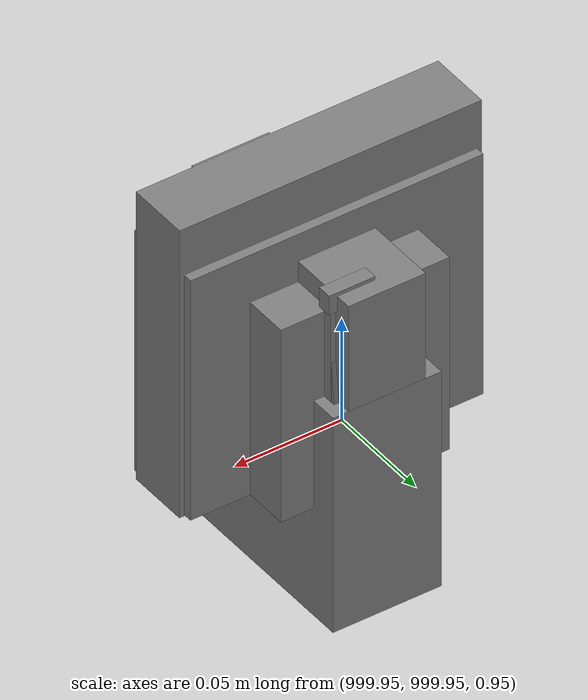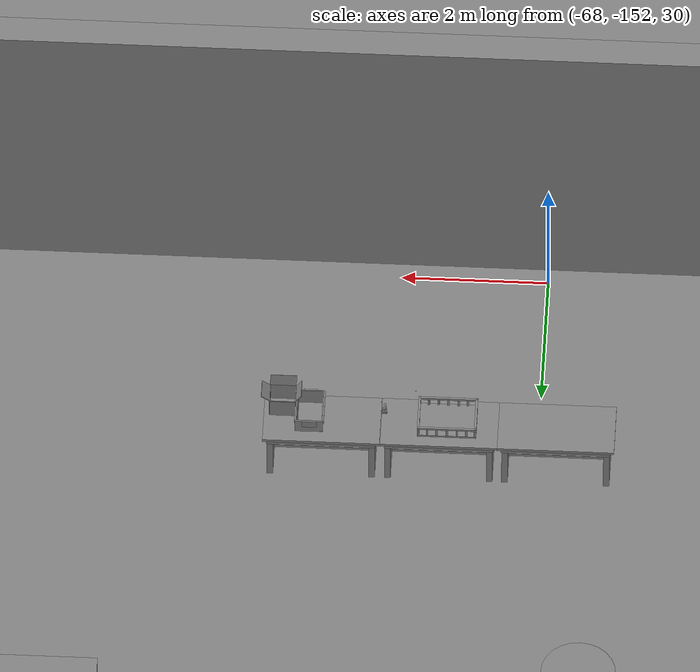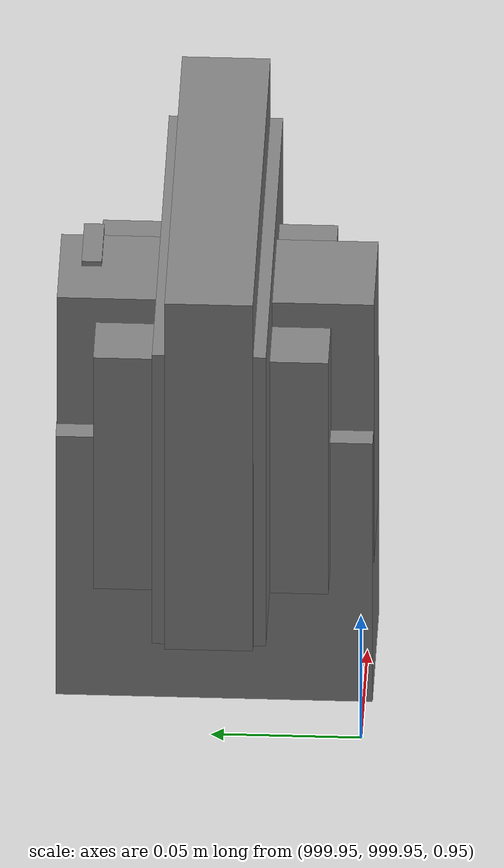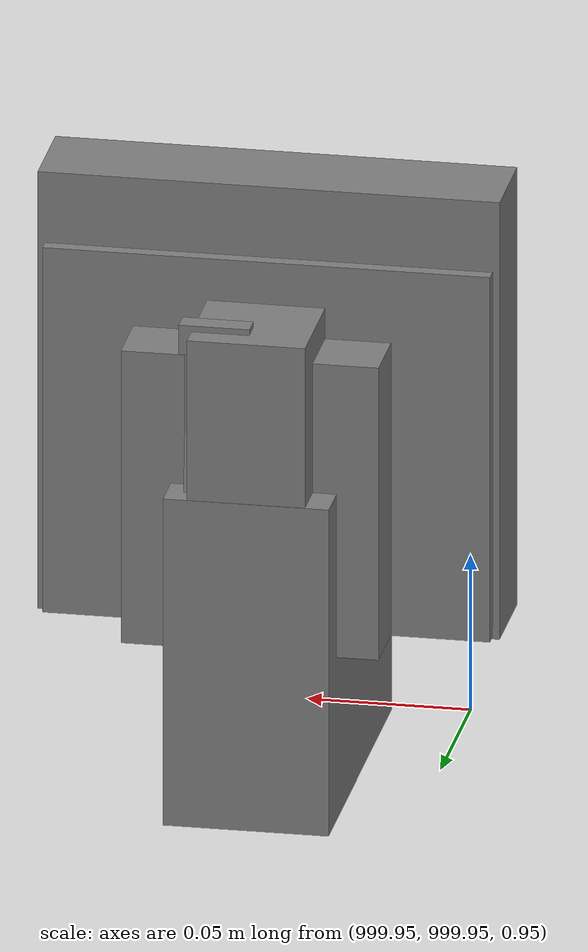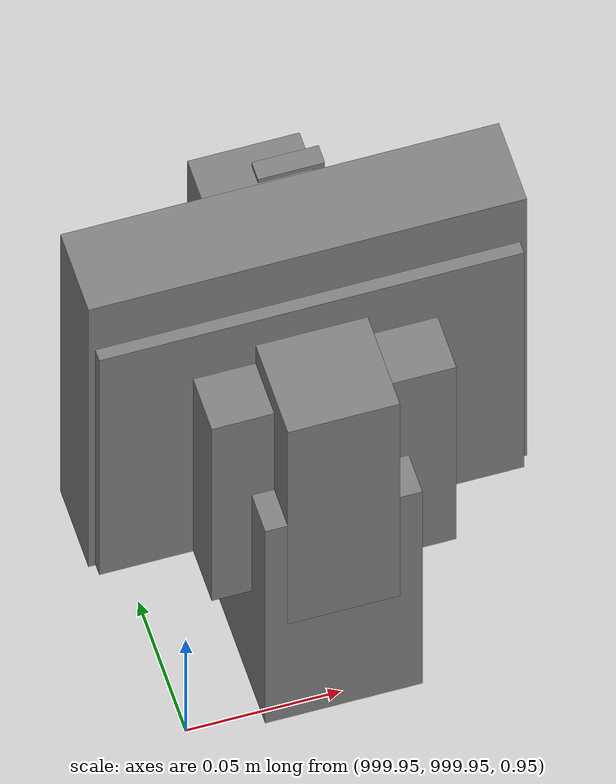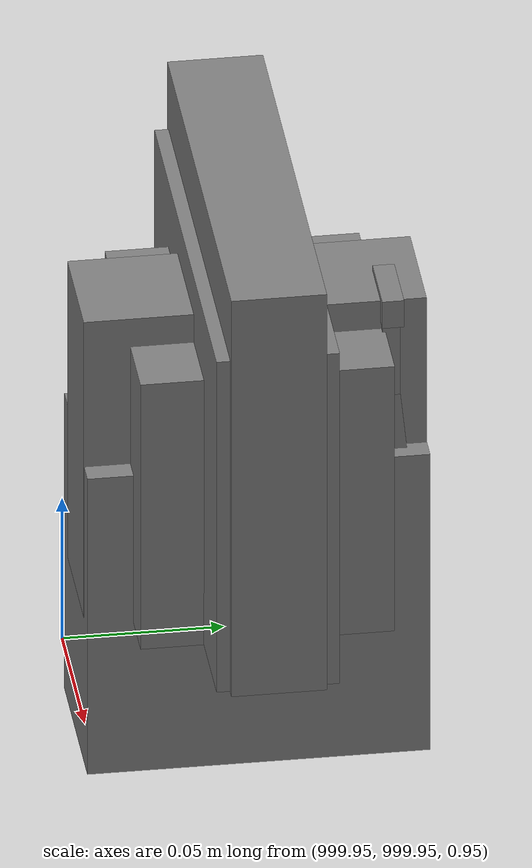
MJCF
<mujoco>
    <option gravity="0.000000000 0.000000000 -9.810000420" timestep="0.0049999999" integrator="implicitfast" density="1.225" viscosity="1.8000001e-05" noslip_iterations="10" iterations="100" sdf_iterations="50">
        <flag multiccd="disable"/>
    </option>
    <size memory="1000M"/>
    <compiler coordinate="local"/>
    <worldbody>
        <light cutoff="30" pos="0 1 1" dir="0 -1 -2"/>
        <light cutoff="30" pos="0 -1 1" dir="0 1 -2"/>
        <body pos="-65.903816223 -148.953964233 31.170257568" euler="51.296428680 16.381906509 -96.714187622" mocap="true" name="spotlight4_SpotLight"/>
        <body pos="1000.000000000 1000.000000000 1.000000000" euler="0.000000000 0.000000000 180.000000000" name="openloong_gripper_2f85_fix_base_usda_battery_01">
            <geom contype="1" conaffinity="1" density="1000" type="box" material="" rgba="0.500000000 0.500000000 0.500000000 1.000000000" solimp="0.899999976 0.949999988 0.001000000" friction="1.000000000 0.005000000 0.000100000" solref="0.020000000 1.000000000" margin="0" condim="3" group="0" pos="-0.011123657 -0.041940309 0.101691343" quat="1.000000000 0.000000000 0.000000000 0.000000000" size="0.010800000 0.003375000 0.004725000" name="openloong_gripper_2f85_fix_base_usda_geom_7AC98E5D_066A_460C_BBD2_3DCA037274ED"/>
            <geom contype="1" conaffinity="1" density="1000" type="box" material="" rgba="0.500000000 0.500000000 0.500000000 1.000000000" solimp="0.899999976 0.949999988 0.001000000" friction="1.000000000 0.005000000 0.000100000" solref="0.020000000 1.000000000" margin="0" condim="3" group="0" pos="-0.010876465 -0.044247437 0.047066893" quat="0.998702705 -0.050920475 0.000000000 0.000000000" size="0.009450001 0.002700000 0.024975000" name="openloong_gripper_2f85_fix_base_usda_geom_1C8563A1_EEA2_497C_BFBB_9969E9DFC381"/>
            <geom contype="1" conaffinity="1" density="1000" type="box" material="" rgba="0.500000000 0.500000000 0.500000000 1.000000000" solimp="0.899999976 0.949999988 0.001000000" friction="1.000000000 0.005000000 0.000100000" solref="0.020000000 1.000000000" margin="0" condim="3" group="0" pos="-0.001235962 -0.000659180 0.047381196" quat="1.000000000 0.000000000 0.000000000 0.000000000" size="0.039420001 0.039150000 0.047250003" name="openloong_gripper_2f85_fix_base_usda_geom_2C4D5716_98FB_4804_8DCB_EA5752A22E32"/>
            <geom contype="1" conaffinity="1" density="1000" type="box" material="" rgba="0.500000000 0.500000000 0.500000000 1.000000000" solimp="0.899999976 0.949999988 0.001000000" friction="1.000000000 0.005000000 0.000100000" solref="0.020000000 1.000000000" margin="0" condim="3" group="0" pos="-0.010876465 -0.039138794 0.009851727" quat="1.000000000 0.000000000 0.000000000 0.000000000" size="0.009450001 0.010800000 0.013500000" name="openloong_gripper_2f85_fix_base_usda_geom_455CEBA8_1CC2_4D24_BB1E_D95D5B5BEC4B"/>
            <geom contype="1" conaffinity="1" density="1000" type="box" material="" rgba="0.500000000 0.500000000 0.500000000 1.000000000" solimp="0.899999976 0.949999988 0.001000000" friction="1.000000000 0.005000000 0.000100000" solref="0.020000000 1.000000000" margin="0" condim="3" group="0" pos="-0.010876465 -0.041528322 0.071508206" quat="1.000000000 0.000000000 0.000000000 0.000000000" size="0.009450001 0.002700000 0.027000001" name="openloong_gripper_2f85_fix_base_usda_geom_45FCA7C3_B238_4B1C_B665_EF15BC45615F"/>
            <freejoint name="openloong_gripper_2f85_fix_base_usda_battery_01_joint"/>
            <site size="0.005000000 0.005000000 0.005000000" rgba="0.500000000 0.500000000 0.500000000 1.000000000" pos="0.000000000 0.000000000 0.000000000" quat="0.999961913 0.008726500 0.000000000 0.000000000" group="0" type="sphere" name="openloong_gripper_2f85_fix_base_usda_battery_01site"/>
        </body>
        <body pos="1000.000000000 1000.000000000 1.000000000" euler="0.000000000 0.000000000 180.000000000" name="openloong_gripper_2f85_fix_base_usda_cpu_fan">
            <geom contype="1" conaffinity="1" density="1000" type="box" material="" rgba="0.500000000 0.500000000 0.500000000 1.000000000" solimp="0.899999976 0.949999988 0.001000000" friction="1.000000000 0.005000000 0.000100000" solref="0.020000000 1.000000000" margin="0" condim="3" group="0" pos="0.000000000 0.000000000 0.070034981" quat="0.000000000 0.000000000 0.000000000 1.000000000" size="0.070700005 0.014699999 0.070700005" name="openloong_gripper_2f85_fix_base_usda_geom_E7AE5B11_9FB6_4AAC_AE6B_16D1B5D6FDD7"/>
            <freejoint name="openloong_gripper_2f85_fix_base_usda_cpu_fan_joint"/>
            <site size="0.005000000 0.005000000 0.005000000" rgba="0.500000000 0.500000000 0.500000000 1.000000000" pos="0.000000000 0.000000000 0.000000000" quat="0.999961913 0.008726535 0.000000000 0.000000000" group="0" type="sphere" name="openloong_gripper_2f85_fix_base_usda_cpu_fancsite"/>
        </body>
        <body pos="1000.000000000 1000.000000000 1.000000000" euler="0.000000000 0.000000000 180.000000000" name="openloong_gripper_2f85_fix_base_usda_wifi_box">
            <geom contype="1" conaffinity="1" density="1000" type="box" material="" rgba="0.500000000 0.500000000 0.500000000 1.000000000" solimp="0.899999976 0.949999988 0.001000000" friction="1.000000000 0.005000000 0.000100000" solref="0.020000000 1.000000000" margin="0" condim="3" group="0" pos="0.000000000 0.000000000 0.058978677" quat="0.000000000 0.000000047 0.000000000 1.000000000" size="0.068499997 0.018999999 0.059000000" name="openloong_gripper_2f85_fix_base_usda_geom_778187F4_6770_4048_9995_E8B1802B9DFC"/>
            <freejoint name="openloong_gripper_2f85_fix_base_usda_wifi_box_joint"/>
            <site size="0.005000000 0.005000000 0.005000000" rgba="0.500000000 0.500000000 0.500000000 1.000000000" pos="0.000000000 0.000000000 0.000000000" quat="0.999961913 0.008726500 0.000000000 0.000000000" group="0" type="sphere" name="openloong_gripper_2f85_fix_base_usda_wifi_boxsite"/>
        </body>
        <body pos="1000.000000000 1000.000000000 1.000000000" euler="0.000011953 0.000005123 -179.999984741" name="openloong_gripper_2f85_fix_base_usda_intel_box">
            <geom contype="1" conaffinity="1" density="1000" type="box" material="" rgba="0.500000000 0.500000000 0.500000000 1.000000000" solimp="0.899999976 0.949999988 0.001000000" friction="1.000000000 0.005000000 0.000100000" solref="0.020000000 1.000000000" margin="0" condim="3" group="0" pos="0.000000000 -0.000067139 0.000082284" quat="0.707106709 0.000000225 0.000000253 0.707106650" size="0.052800003 0.025300000 0.052800003" name="openloong_gripper_2f85_fix_base_usda_geom_E2651459_222A_4845_A801_1D87AAF3B00C"/>
            <freejoint name="openloong_gripper_2f85_fix_base_usda_intel_box_joint"/>
            <site size="0.005000000 0.005000000 0.005000000" rgba="0.500000000 0.500000000 0.500000000 1.000000000" pos="0.000000000 0.000000000 0.000000000" quat="0.999961913 0.008726500 0.000000000 0.000000000" group="0" type="sphere" name="openloong_gripper_2f85_fix_base_usda_intel_boxsite"/>
        </body>
        <body pos="-66.297309875 -149.673934937 31.164844513" euler="-68.403602600 72.497817993 39.453453064" mocap="true" name="spotlight5_SpotLight"/>
        <body pos="1000.000000000 999.999938965 1.000000000" euler="0.000000000 0.000000000 180.000000000" name="openloong_gripper_2f85_fix_base_usda_intelcore_i5">
            <geom contype="1" conaffinity="1" density="1000" type="box" material="" rgba="0.500000000 0.500000000 0.500000000 1.000000000" solimp="0.899999976 0.949999988 0.001000000" friction="1.000000000 0.005000000 0.000100000" solref="0.020000000 1.000000000" margin="0" condim="3" group="0" pos="0.000000000 0.000000000 0.051722717" quat="0.707106709 0.000000000 0.000000000 -0.707106769" size="0.052800000 0.018080002 0.052800000" name="openloong_gripper_2f85_fix_base_usda_geom_461693A3_D52C_415C_934F_6D9539D74E1A"/>
            <freejoint name="openloong_gripper_2f85_fix_base_usda_intelcore_i5_joint"/>
            <site size="0.005000000 0.005000000 0.005000000" rgba="0.500000000 0.500000000 0.500000000 1.000000000" pos="0.000000000 0.000000000 0.000000000" quat="0.999961913 0.008726534 0.000000000 0.000000000" group="0" type="sphere" name="openloong_gripper_2f85_fix_base_usda_intelcore_i5site"/>
        </body>
        <body pos="-66.148857117 -149.706253052 31.168527603" euler="158.148635864 61.584163666 -132.863891602" mocap="true" name="spotlight2_SpotLight"/>
        <body pos="-64.866622925 -149.383972168 30.183746338" euler="89.999984741 89.999946594 0.000000000" name="openloong_gripper_2f85_fix_base_usda_bluebox_01">
            <geom contype="1" conaffinity="1" density="1000" type="box" material="" rgba="0.500000000 0.500000000 0.500000000 1.000000000" solimp="0.899999976 0.949999988 0.001000000" friction="1.000000000 0.005000000 0.000100000" solref="0.020000000 1.000000000" margin="0" condim="3" group="0" pos="0.276580811 0.187225342 0.000068665" quat="0.707106948 0.000077471 0.707106352 0.000077486" size="0.100000001 0.057999998 0.010000000" name="openloong_gripper_2f85_fix_base_usda_geom_177CBF9B_F0C1_4CAB_B5AD_289068F20356"/>
            <geom contype="1" conaffinity="1" density="1000" type="box" material="" rgba="0.500000000 0.500000000 0.500000000 1.000000000" solimp="0.899999976 0.949999988 0.001000000" friction="1.000000000 0.005000000 0.000100000" solref="0.020000000 1.000000000" margin="0" condim="3" group="0" pos="0.000000000 0.002883911 0.000000000" quat="0.999999881 0.000000000 0.000000000 0.000000000" size="0.254000008 0.003000000 0.172000006" name="openloong_gripper_2f85_fix_base_usda_geom_C4EEA8BE_592E_4521_86D4_CDAA21FF282A"/>
            <geom contype="1" conaffinity="1" density="1000" type="box" material="" rgba="0.500000000 0.500000000 0.500000000 1.000000000" solimp="0.899999976 0.949999988 0.001000000" friction="1.000000000 0.005000000 0.000100000" solref="0.020000000 1.000000000" margin="0" condim="3" group="0" pos="0.000000000 0.124874115 0.173484802" quat="0.999796331 0.020176515 -0.000000015 0.000000030" size="0.259999990 0.119999997 0.007000000" name="openloong_gripper_2f85_fix_base_usda_geom_28C2F364_69E5_42AC_9A86_FAA2576751F5"/>
            <geom contype="1" conaffinity="1" density="1000" type="box" material="" rgba="0.500000000 0.500000000 0.500000000 1.000000000" solimp="0.899999976 0.949999988 0.001000000" friction="1.000000000 0.005000000 0.000100000" solref="0.020000000 1.000000000" margin="0" condim="3" group="0" pos="0.000000000 0.124874115 -0.173469543" quat="0.999796331 -0.020176545 -0.000000015 0.000000000" size="0.259999990 0.119999997 0.007000000" name="openloong_gripper_2f85_fix_base_usda_geom_11062471_994C_4E46_8A9B_BF618E5880D0"/>
            <geom contype="1" conaffinity="1" density="1000" type="box" material="" rgba="0.500000000 0.500000000 0.500000000 1.000000000" solimp="0.899999976 0.949999988 0.001000000" friction="1.000000000 0.005000000 0.000100000" solref="0.020000000 1.000000000" margin="0" condim="3" group="0" pos="0.000000000 0.214008331 0.188980103" quat="0.999912977 0.013176724 0.000000015 0.000000000" size="0.259999990 0.029999999 0.012500000" name="openloong_gripper_2f85_fix_base_usda_geom_49B5C7B3_812E_4C76_AA35_07C9920C7BEE"/>
            <geom contype="1" conaffinity="1" density="1000" type="box" material="" rgba="0.500000000 0.500000000 0.500000000 1.000000000" solimp="0.899999976 0.949999988 0.001000000" friction="1.000000000 0.005000000 0.000100000" solref="0.020000000 1.000000000" margin="0" condim="3" group="0" pos="-0.258361816 0.125289917 0.001876831" quat="0.702796936 -0.020792112 0.710783124 0.020769298" size="0.189999998 0.119999997 0.009000000" name="openloong_gripper_2f85_fix_base_usda_geom_0E1E6FDB_090B_4835_B629_C7B1759F90BA"/>
            <geom contype="1" conaffinity="1" density="1000" type="box" material="" rgba="0.500000000 0.500000000 0.500000000 1.000000000" solimp="0.899999976 0.949999988 0.001000000" friction="1.000000000 0.005000000 0.000100000" solref="0.020000000 1.000000000" margin="0" condim="3" group="0" pos="0.000000000 0.214008331 -0.188980103" quat="0.999912977 -0.013176769 0.000000030 0.000000015" size="0.259999990 0.029999999 0.012500000" name="openloong_gripper_2f85_fix_base_usda_geom_E1C4BD45_9450_4E37_9A9B_091926BBA014"/>
            <geom contype="1" conaffinity="1" density="1000" type="box" material="" rgba="0.500000000 0.500000000 0.500000000 1.000000000" solimp="0.899999976 0.949999988 0.001000000" friction="1.000000000 0.005000000 0.000100000" solref="0.020000000 1.000000000" margin="0" condim="3" group="0" pos="-0.276611328 0.187225342 0.000068665" quat="0.707106650 0.000077441 0.707106709 0.000077456" size="0.100000001 0.057999998 0.010000000" name="openloong_gripper_2f85_fix_base_usda_geom_F245BD81_81E1_4A9A_8C4C_1F0D25C69144"/>
            <geom contype="1" conaffinity="1" density="1000" type="box" material="" rgba="0.500000000 0.500000000 0.500000000 1.000000000" solimp="0.899999976 0.949999988 0.001000000" friction="1.000000000 0.005000000 0.000100000" solref="0.020000000 1.000000000" margin="0" condim="3" group="0" pos="0.258331299 0.125289917 0.001876831" quat="0.702851415 0.018856421 0.710823774 -0.019329369" size="0.189999998 0.119999997 0.009000000" name="openloong_gripper_2f85_fix_base_usda_geom_1E775044_6791_46A2_BC66_D4471250E9C9"/>
            <freejoint name="openloong_gripper_2f85_fix_base_usda_bluebox_01_joint"/>
            <site size="0.005000000 0.005000000 0.005000000" rgba="0.500000000 0.500000000 0.500000000 1.000000000" pos="0.000000000 0.000000000 0.000000000" quat="0.999961913 0.008726534 0.000000000 0.000000000" group="0" type="sphere" name="openloong_gripper_2f85_fix_base_usda_bluebox_01site"/>
        </body>
        <body pos="-64.496299744 -149.491867065 30.235729218" euler="0.000000000 0.000000000 89.999946594" name="openloong_gripper_2f85_fix_base_usda_cardboardbox_01">
            <geom contype="1" conaffinity="1" density="1000" type="box" material="" rgba="0.500000000 0.500000000 0.500000000 1.000000000" solimp="0.899999976 0.949999988 0.001000000" friction="1.000000000 0.005000000 0.000100000" solref="0.020000000 1.000000000" margin="0" condim="3" group="0" pos="-0.003166199 -0.004086494 0.005052090" quat="1.000000000 0.000000000 0.000000000 0.000000000" size="0.142499998 0.177500010 0.005000000" name="openloong_gripper_2f85_fix_base_usda_geom_FABC42C9_7850_4899_8185_F5470541AA79"/>
            <geom contype="1" conaffinity="1" density="1000" type="box" material="" rgba="0.500000000 0.500000000 0.500000000 1.000000000" solimp="0.899999976 0.949999988 0.001000000" friction="1.000000000 0.005000000 0.000100000" solref="0.020000000 1.000000000" margin="0" condim="3" group="0" pos="-0.003166199 0.170316696 0.150570869" quat="1.000000000 0.000000000 0.000000000 0.000000000" size="0.142499998 0.005000000 0.149999991" name="openloong_gripper_2f85_fix_base_usda_geom_7183CF37_03C8_45C8_B812_9E71B7AB1CE1"/>
            <geom contype="1" conaffinity="1" density="1000" type="box" material="" rgba="0.500000000 0.500000000 0.500000000 1.000000000" solimp="0.899999976 0.949999988 0.001000000" friction="1.000000000 0.005000000 0.000100000" solref="0.020000000 1.000000000" margin="0" condim="3" group="0" pos="-0.147399902 -0.005307198 0.150570869" quat="1.000000000 0.000000000 0.000000000 0.000000000" size="0.005000000 0.177500010 0.149999991" name="openloong_gripper_2f85_fix_base_usda_geom_B4D63EAB_4E37_435C_8372_8A936E0AC813"/>
            <geom contype="1" conaffinity="1" density="1000" type="box" material="" rgba="0.500000000 0.500000000 0.500000000 1.000000000" solimp="0.899999976 0.949999988 0.001000000" friction="1.000000000 0.005000000 0.000100000" solref="0.020000000 1.000000000" margin="0" condim="3" group="0" pos="0.140275955 -0.005307198 0.150570869" quat="1.000000000 0.000000000 0.000000000 0.000000000" size="0.005000000 0.177500010 0.149999991" name="openloong_gripper_2f85_fix_base_usda_geom_712E6402_9C72_4CC6_867E_C418C29BAE52"/>
            <geom contype="1" conaffinity="1" density="1000" type="box" material="" rgba="0.500000000 0.500000000 0.500000000 1.000000000" solimp="0.899999976 0.949999988 0.001000000" friction="1.000000000 0.005000000 0.000100000" solref="0.020000000 1.000000000" margin="0" condim="3" group="0" pos="-0.003166199 -0.181550980 0.150570869" quat="1.000000000 0.000000000 0.000000000 0.000000000" size="0.142499998 0.005000000 0.149999991" name="openloong_gripper_2f85_fix_base_usda_geom_95B24BF8_2DE3_4966_9195_05BB86E82448"/>
            <freejoint name="openloong_gripper_2f85_fix_base_usda_cardboardbox_01_joint"/>
            <site size="0.005000000 0.005000000 0.005000000" rgba="0.500000000 0.500000000 0.500000000 1.000000000" pos="0.000000000 0.000000000 0.000000000" quat="0.999961913 0.008726535 0.000000000 0.000000000" group="0" type="sphere" name="openloong_gripper_2f85_fix_base_usda_site_71295638_5211_4B3C_BD01_6F7CAC82B986"/>
            <body pos="0.139160156 -0.004048347 0.301930904" euler="-179.999954224 49.383502960 179.999954224" name="openloong_gripper_2f85_fix_base_usda_A1_006">
                <geom contype="1" conaffinity="1" density="1000" type="box" material="" rgba="0.500000000 0.500000000 0.500000000 1.000000000" solimp="0.899999976 0.949999988 0.001000000" friction="1.000000000 0.005000000 0.000100000" solref="0.020000000 1.000000000" margin="0" condim="3" group="0" pos="-0.071587563 0.000009537 0.001745224" quat="0.999999881 0.000000000 0.000000000 0.000000000" size="0.071249999 0.179999992 0.002500000" name="openloong_gripper_2f85_fix_base_usda_geom_FF9D14B3_5148_457C_8B72_912F56AB2A25"/>
                <joint armature="0" stiffness="0.07" damping="0.0099999998" axis="0.000000 1.000000 0.000000" type="hinge" name="openloong_gripper_2f85_fix_base_usda_A1_006"/>
            </body>
            <body pos="-0.145902634 -0.004086494 0.301938057" euler="-180.000000000 -60.000011444 -180.000000000" name="openloong_gripper_2f85_fix_base_usda_A2_006">
                <geom contype="1" conaffinity="1" density="1000" type="box" material="" rgba="0.500000000 0.500000000 0.500000000 1.000000000" solimp="0.899999976 0.949999988 0.001000000" friction="1.000000000 0.005000000 0.000100000" solref="0.020000000 1.000000000" margin="0" condim="3" group="0" pos="0.071268082 0.000009537 0.002717972" quat="0.000002921 0.000000000 -0.000000030 0.999999881" size="0.071249999 0.179999992 0.002500000" name="openloong_gripper_2f85_fix_base_usda_geom_0DA62045_DF7B_497D_BEB0_A5838791557E"/>
                <joint armature="0" stiffness="0.07" damping="0.0099999998" axis="0.000000 1.000000 0.000000" type="hinge" name="openloong_gripper_2f85_fix_base_usda_A2_006"/>
            </body>
            <body pos="-0.003385544 0.175991058 0.301930904" euler="-125.858116150 -0.000004561 0.000002331" name="openloong_gripper_2f85_fix_base_usda_B2_006">
                <geom contype="1" conaffinity="1" density="1000" type="box" material="" rgba="0.500000000 0.500000000 0.500000000 1.000000000" solimp="0.899999976 0.949999988 0.001000000" friction="1.000000000 0.005000000 0.000100000" solref="0.020000000 1.000000000" margin="0" condim="3" group="0" pos="0.000009537 -0.070939064 -0.002470016" quat="0.999614120 0.027776197 -0.000000015 0.000000030" size="0.137500003 0.064999998 0.005000000" name="openloong_gripper_2f85_fix_base_usda_geom_B4280653_2065_47C7_9709_C2E188CFF35D"/>
                <joint armature="0" stiffness="0.07" damping="0.0099999998" axis="1.000000 0.000000 0.000000" type="hinge" name="openloong_gripper_2f85_fix_base_usda_B2_006"/>
            </body>
            <body pos="-0.003385544 -0.184140205 0.301938057" euler="147.805557251 0.000000000 0.000000000" name="openloong_gripper_2f85_fix_base_usda_B1_006">
                <geom contype="1" conaffinity="1" density="1000" type="box" material="" rgba="0.500000000 0.500000000 0.500000000 1.000000000" solimp="0.899999976 0.949999988 0.001000000" friction="1.000000000 0.005000000 0.000100000" solref="0.020000000 1.000000000" margin="0" condim="3" group="0" pos="-0.000028610 0.070202351 -0.002703667" quat="0.999614179 -0.027776167 0.000000000 0.000000000" size="0.137500003 0.064999998 0.005000000" name="openloong_gripper_2f85_fix_base_usda_geom_F3EAEFB0_5CB2_44E8_8828_FEB70FB113A2"/>
                <joint armature="0" stiffness="0.07" damping="0.0099999998" axis="1.000000 0.000000 0.000000" type="hinge" name="openloong_gripper_2f85_fix_base_usda_B1_006"/>
            </body>
        </body>
        <body pos="-65.882858276 -149.481979370 30.229999542" euler="-64.487716675 0.000000000 0.000000000" name="openloong_gripper_2f85_fix_base_usda_Barcode">
            <geom contype="1" conaffinity="1" density="1000" type="box" material="" rgba="0.500000000 0.500000000 0.500000000 1.000000000" solimp="0.899999976 0.949999988 0.001000000" friction="1.000000000 0.005000000 0.000100000" solref="0.020000000 1.000000000" margin="0" condim="3" group="0" pos="0.000000000 0.013038635 0.001419067" quat="0.000000000 0.000000000 0.000000000 1.000000119" size="0.034000002 0.010000000 0.017999999" name="openloong_gripper_2f85_fix_base_usda_geom_2469E4CB_003D_415C_8972_678AE5ACA9CD"/>
            <geom contype="1" conaffinity="1" density="1000" type="box" material="" rgba="0.500000000 0.500000000 0.500000000 1.000000000" solimp="0.899999976 0.949999988 0.001000000" friction="1.000000000 0.005000000 0.000100000" solref="0.020000000 1.000000000" margin="0" condim="3" group="0" pos="0.000000000 -0.035301208 -0.007095337" quat="0.000000000 0.000000000 -0.043619365 0.999048233" size="0.028999999 0.010000000 0.020000000" name="openloong_gripper_2f85_fix_base_usda_geom_C7B2FAA0_61AC_4504_BE29_B43144E3DBA5"/>
            <geom contype="1" conaffinity="1" density="1000" type="box" material="" rgba="0.500000000 0.500000000 0.500000000 1.000000000" solimp="0.899999976 0.949999988 0.001000000" friction="1.000000000 0.005000000 0.000100000" solref="0.020000000 1.000000000" margin="0" condim="3" group="0" pos="0.000000000 -0.043411255 -0.011749268" quat="0.922262907 0.386563420 0.000000000 0.000000000" size="0.026000001 0.010000000 0.020000000" name="openloong_gripper_2f85_fix_base_usda_geom_B4499089_5C16_49EF_9380_C3857F0FF8E3"/>
            <geom contype="1" conaffinity="1" density="1000" type="box" material="" rgba="0.500000000 0.500000000 0.500000000 1.000000000" solimp="0.899999976 0.949999988 0.001000000" friction="1.000000000 0.005000000 0.000100000" solref="0.020000000 1.000000000" margin="0" condim="3" group="0" pos="0.000000000 -0.016967773 -0.031860352" quat="0.000000000 0.000000000 0.000000000 1.000000119" size="0.008000000 0.010000000 0.013000000" name="openloong_gripper_2f85_fix_base_usda_geom_F7637097_F483_49EA_947B_E2AA1CD6A768"/>
            <geom contype="1" conaffinity="1" density="1000" type="box" material="" rgba="0.500000000 0.500000000 0.500000000 1.000000000" solimp="0.899999976 0.949999988 0.001000000" friction="1.000000000 0.005000000 0.000100000" solref="0.020000000 1.000000000" margin="0" condim="3" group="0" pos="0.000000000 -0.001869202 0.000312805" quat="0.953716993 0.300705761 0.000000000 0.000000000" size="0.032000002 0.010000000 0.018999999" name="openloong_gripper_2f85_fix_base_usda_geom_A1581737_4CBC_48DB_BDA3_B5D689147D33"/>
            <geom contype="1" conaffinity="1" density="1000" type="box" material="" rgba="0.500000000 0.500000000 0.500000000 1.000000000" solimp="0.899999976 0.949999988 0.001000000" friction="1.000000000 0.005000000 0.000100000" solref="0.020000000 1.000000000" margin="0" condim="3" group="0" pos="0.000000000 -0.019531250 -0.003173828" quat="0.953716993 0.300705761 0.000000000 0.000000000" size="0.030999999 0.010000000 0.020000000" name="openloong_gripper_2f85_fix_base_usda_geom_1FF276C7_3569_42E9_AA62_FE107430D5F7"/>
            <geom contype="1" conaffinity="1" density="1000" type="box" material="" rgba="0.500000000 0.500000000 0.500000000 1.000000000" solimp="0.899999976 0.949999988 0.001000000" friction="1.000000000 0.005000000 0.000100000" solref="0.020000000 1.000000000" margin="0" condim="3" group="0" pos="0.000000000 -0.035301208 -0.007095337" quat="0.953716993 0.300705761 0.000000000 0.000000000" size="0.028999999 0.010000000 0.020000000" name="openloong_gripper_2f85_fix_base_usda_geom_C6F9D0A5_AD27_43DF_95D3_2BC9422C6121"/>
            <geom contype="1" conaffinity="1" density="1000" type="box" material="" rgba="0.500000000 0.500000000 0.500000000 1.000000000" solimp="0.899999976 0.949999988 0.001000000" friction="1.000000000 0.005000000 0.000100000" solref="0.020000000 1.000000000" margin="0" condim="3" group="0" pos="0.000000000 -0.042617798 -0.071121216" quat="0.000000000 0.000000000 0.000000000 1.000000119" size="0.013000000 0.021000000 0.059999999" name="openloong_gripper_2f85_fix_base_usda_geom_23C38A9E_095E_4A60_B98A_9DDABE593748"/>
            <freejoint name="openloong_gripper_2f85_fix_base_usda_Barcode_joint"/>
            <site size="0.005000000 0.005000000 0.005000000" rgba="0.500000000 0.500000000 0.500000000 1.000000000" pos="0.000000000 0.000000000 0.000000000" quat="1.000000000 0.000000000 0.000000000 0.000000000" group="0" type="sphere" name="openloong_gripper_2f85_fix_base_usda_Barcode_site"/>
        </body>
        <body pos="-66.745018005 -149.392349243 30.184000015" euler="0.000000000 0.000000000 89.999946594" name="[22330368393480]_Basket_01">
            <geom contype="1" conaffinity="1" density="1000" type="box" material="" rgba="0.500000000 0.500000000 0.500000000 1.000000000" solimp="0.899999976 0.949999988 0.001000000" friction="1.000000000 0.005000000 0.000100000" solref="0.020000000 1.000000000" margin="0" condim="3" group="0" pos="-0.052425385 0.389207840 0.089787483" quat="0.707107008 0.000000000 0.000000000 0.707106411" size="0.014249999 0.014249999 0.059999999" name="[22330368393480]_geom_EEB954BC_EEED_448D_81D7_F14C9DF0BD51"/>
            <geom contype="1" conaffinity="1" density="1000" type="box" material="" rgba="0.500000000 0.500000000 0.500000000 1.000000000" solimp="0.899999976 0.949999988 0.001000000" friction="1.000000000 0.005000000 0.000100000" solref="0.020000000 1.000000000" margin="0" condim="3" group="0" pos="0.264015198 -0.133043289 0.089787483" quat="0.707107008 0.000000000 0.000000000 0.707106411" size="0.014249999 0.014249999 0.059999999" name="[22330368393480]_geom_4EAC66E3_1A77_4913_A0BE_7EA41BF11F5D"/>
            <geom contype="1" conaffinity="1" density="1000" type="box" material="" rgba="0.500000000 0.500000000 0.500000000 1.000000000" solimp="0.899999976 0.949999988 0.001000000" friction="1.000000000 0.005000000 0.000100000" solref="0.020000000 1.000000000" margin="0" condim="3" group="0" pos="-0.264015198 -0.265548706 0.089793205" quat="0.707107008 0.000000000 0.000000000 0.707106411" size="0.014249999 0.014249999 0.059999999" name="[22330368393480]_geom_F5B2DBBF_BE8C_4014_826D_5F6D1CE36474"/>
            <geom contype="1" conaffinity="1" density="1000" type="box" material="" rgba="0.500000000 0.500000000 0.500000000 1.000000000" solimp="0.899999976 0.949999988 0.001000000" friction="1.000000000 0.005000000 0.000100000" solref="0.020000000 1.000000000" margin="0" condim="3" group="0" pos="-0.160263062 -0.389322281 0.089793205" quat="0.707107008 0.000000000 0.000000000 0.707106411" size="0.014249999 0.014249999 0.059999999" name="[22330368393480]_geom_A4DD6F12_9BE6_4B74_9813_21F7C8833A4B"/>
            <geom contype="1" conaffinity="1" density="1000" type="box" material="" rgba="0.500000000 0.500000000 0.500000000 1.000000000" solimp="0.899999976 0.949999988 0.001000000" friction="1.000000000 0.005000000 0.000100000" solref="0.020000000 1.000000000" margin="0" condim="3" group="0" pos="0.162265778 -0.389322281 0.089787483" quat="0.707107008 0.000000000 0.000000000 0.707106411" size="0.014249999 0.014249999 0.059999999" name="[22330368393480]_geom_6E3A9883_7AAA_46CD_8A79_3D1336DA80AA"/>
            <geom contype="1" conaffinity="1" density="1000" type="box" material="" rgba="0.500000000 0.500000000 0.500000000 1.000000000" solimp="0.899999976 0.949999988 0.001000000" friction="1.000000000 0.005000000 0.000100000" solref="0.020000000 1.000000000" margin="0" condim="3" group="0" pos="0.264015198 0.389207840 0.089787483" quat="0.707107008 0.000000000 0.000000000 0.707106411" size="0.014249999 0.014249999 0.059999999" name="[22330368393480]_geom_EDEC5317_22DA_4B6B_8C16_0A6844A73301"/>
            <geom contype="1" conaffinity="1" density="1000" type="box" material="" rgba="0.500000000 0.500000000 0.500000000 1.000000000" solimp="0.899999976 0.949999988 0.001000000" friction="1.000000000 0.005000000 0.000100000" solref="0.020000000 1.000000000" margin="0" condim="3" group="0" pos="-0.264015198 -0.133043289 0.089793205" quat="0.707107008 0.000000000 0.000000000 0.707106411" size="0.014249999 0.014249999 0.059999999" name="[22330368393480]_geom_EC94B22B_8EB4_484F_9920_5C09BE9BE2AC"/>
            <geom contype="1" conaffinity="1" density="1000" type="box" material="" rgba="0.500000000 0.500000000 0.500000000 1.000000000" solimp="0.899999976 0.949999988 0.001000000" friction="1.000000000 0.005000000 0.000100000" solref="0.020000000 1.000000000" margin="0" condim="3" group="0" pos="-0.264026642 0.269256592 0.089793205" quat="0.707107008 0.000000000 0.000000000 0.707106411" size="0.014249999 0.014249999 0.059999999" name="[22330368393480]_geom_C3518267_A542_4C54_B00A_E83FC68971BE"/>
            <geom contype="1" conaffinity="1" density="1000" type="box" material="" rgba="0.500000000 0.500000000 0.500000000 1.000000000" solimp="0.899999976 0.949999988 0.001000000" friction="1.000000000 0.005000000 0.000100000" solref="0.020000000 1.000000000" margin="0" condim="3" group="0" pos="0.054462433 0.389207840 0.089787483" quat="0.707107008 0.000000000 0.000000000 0.707106411" size="0.014249999 0.014249999 0.059999999" name="[22330368393480]_geom_B47326FA_5324_4699_A29C_B49C9BCE454A"/>
            <geom contype="1" conaffinity="1" density="1000" type="box" material="" rgba="0.500000000 0.500000000 0.500000000 1.000000000" solimp="0.899999976 0.949999988 0.001000000" friction="1.000000000 0.005000000 0.000100000" solref="0.020000000 1.000000000" margin="0" condim="3" group="0" pos="0.054462433 -0.389322281 0.089787483" quat="0.707107008 0.000000000 0.000000000 0.707106411" size="0.014249999 0.014249999 0.059999999" name="[22330368393480]_geom_F41B49C1_5D35_488D_95B8_295DD0FD50AB"/>
            <geom contype="1" conaffinity="1" density="1000" type="box" material="" rgba="0.500000000 0.500000000 0.500000000 1.000000000" solimp="0.899999976 0.949999988 0.001000000" friction="1.000000000 0.005000000 0.000100000" solref="0.020000000 1.000000000" margin="0" condim="3" group="0" pos="0.264015198 0.269256592 0.089793205" quat="0.707107008 0.000000000 0.000000000 0.707106411" size="0.014249999 0.014249999 0.059999999" name="[22330368393480]_geom_BCD850C4_3918_45FF_8B7B_FB0271E4D829"/>
            <geom contype="1" conaffinity="1" density="1000" type="box" material="" rgba="0.500000000 0.500000000 0.500000000 1.000000000" solimp="0.899999976 0.949999988 0.001000000" friction="1.000000000 0.005000000 0.000100000" solref="0.020000000 1.000000000" margin="0" condim="3" group="0" pos="0.264015198 -0.389322281 0.089787483" quat="0.707107008 0.000000000 0.000000000 0.707106411" size="0.014249999 0.014249999 0.059999999" name="[22330368393480]_geom_9CD84D4B_470D_4DCE_9AFF_41BABC5377A7"/>
            <geom contype="1" conaffinity="1" density="1000" type="box" material="" rgba="0.500000000 0.500000000 0.500000000 1.000000000" solimp="0.899999976 0.949999988 0.001000000" friction="1.000000000 0.005000000 0.000100000" solref="0.020000000 1.000000000" margin="0" condim="3" group="0" pos="0.000000000 0.000000000 0.015998840" quat="0.707107008 0.000000000 0.000000000 0.707106411" size="0.403499991 0.279000014 0.015750000" name="[22330368393480]_geom_50834A8B_B3BD_4260_9FD6_CD8CC61F15BB"/>
            <geom contype="1" conaffinity="1" density="1000" type="box" material="" rgba="0.500000000 0.500000000 0.500000000 1.000000000" solimp="0.899999976 0.949999988 0.001000000" friction="1.000000000 0.005000000 0.000100000" solref="0.020000000 1.000000000" margin="0" condim="3" group="0" pos="0.000000000 -0.389476776 0.163619041" quat="0.707107008 0.000000000 0.000000000 0.707106411" size="0.015000000 0.277500004 0.015750000" name="[22330368393480]_geom_A25DF6FC_AE73_4F5B_9EC4_D75A7AAEE308"/>
            <geom contype="1" conaffinity="1" density="1000" type="box" material="" rgba="0.500000000 0.500000000 0.500000000 1.000000000" solimp="0.899999976 0.949999988 0.001000000" friction="1.000000000 0.005000000 0.000100000" solref="0.020000000 1.000000000" margin="0" condim="3" group="0" pos="0.162265778 0.389207840 0.089787483" quat="0.707107008 0.000000000 0.000000000 0.707106411" size="0.014249999 0.014249999 0.059999999" name="[22330368393480]_geom_9E34003D_885E_48ED_B93B_B9F0B8FE8F1F"/>
            <geom contype="1" conaffinity="1" density="1000" type="box" material="" rgba="0.500000000 0.500000000 0.500000000 1.000000000" solimp="0.899999976 0.949999988 0.001000000" friction="1.000000000 0.005000000 0.000100000" solref="0.020000000 1.000000000" margin="0" condim="3" group="0" pos="0.000000000 0.389471054 0.163619041" quat="0.707107008 0.000000000 0.000000000 0.707106411" size="0.015000000 0.277500004 0.015750000" name="[22330368393480]_geom_5E5386CC_E7C0_44C9_956D_DBA77E4B6981"/>
            <geom contype="1" conaffinity="1" density="1000" type="box" material="" rgba="0.500000000 0.500000000 0.500000000 1.000000000" solimp="0.899999976 0.949999988 0.001000000" friction="1.000000000 0.005000000 0.000100000" solref="0.020000000 1.000000000" margin="0" condim="3" group="0" pos="-0.263511658 0.000000000 0.163619041" quat="0.707107008 0.000000000 0.000000000 0.707106411" size="0.403499991 0.015000000 0.015750000" name="[22330368393480]_geom_A75C3CA9_1DB3_4CCB_9236_E4680DA7932B"/>
            <geom contype="1" conaffinity="1" density="1000" type="box" material="" rgba="0.500000000 0.500000000 0.500000000 1.000000000" solimp="0.899999976 0.949999988 0.001000000" friction="1.000000000 0.005000000 0.000100000" solref="0.020000000 1.000000000" margin="0" condim="3" group="0" pos="-0.264015198 0.141334534 0.089793205" quat="0.707107008 0.000000000 0.000000000 0.707106411" size="0.014249999 0.014249999 0.059999999" name="[22330368393480]_geom_22EFBC6F_272D_4968_9503_0EDFDDE34CFF"/>
            <geom contype="1" conaffinity="1" density="1000" type="box" material="" rgba="0.500000000 0.500000000 0.500000000 1.000000000" solimp="0.899999976 0.949999988 0.001000000" friction="1.000000000 0.005000000 0.000100000" solref="0.020000000 1.000000000" margin="0" condim="3" group="0" pos="0.264015198 -0.265548706 0.089787483" quat="0.707107008 0.000000000 0.000000000 0.707106411" size="0.014249999 0.014249999 0.059999999" name="[22330368393480]_geom_AF2916BF_93E2_4337_9621_50C9D97360CA"/>
            <geom contype="1" conaffinity="1" density="1000" type="box" material="" rgba="0.500000000 0.500000000 0.500000000 1.000000000" solimp="0.899999976 0.949999988 0.001000000" friction="1.000000000 0.005000000 0.000100000" solref="0.020000000 1.000000000" margin="0" condim="3" group="0" pos="-0.160263062 0.389207840 0.089787483" quat="0.707107008 0.000000000 0.000000000 0.707106411" size="0.014249999 0.014249999 0.059999999" name="[22330368393480]_geom_3A885975_B338_43DD_9B0C_5EC94713FA0B"/>
            <geom contype="1" conaffinity="1" density="1000" type="box" material="" rgba="0.500000000 0.500000000 0.500000000 1.000000000" solimp="0.899999976 0.949999988 0.001000000" friction="1.000000000 0.005000000 0.000100000" solref="0.020000000 1.000000000" margin="0" condim="3" group="0" pos="-0.052425385 -0.389322281 0.089787483" quat="0.707107008 0.000000000 0.000000000 0.707106411" size="0.014249999 0.014249999 0.059999999" name="[22330368393480]_geom_F125C602_E2CE_412E_B2E1_93E1EA6EA841"/>
            <geom contype="1" conaffinity="1" density="1000" type="box" material="" rgba="0.500000000 0.500000000 0.500000000 1.000000000" solimp="0.899999976 0.949999988 0.001000000" friction="1.000000000 0.005000000 0.000100000" solref="0.020000000 1.000000000" margin="0" condim="3" group="0" pos="-0.264026642 -0.389322281 0.089793205" quat="0.707107008 0.000000000 0.000000000 0.707106411" size="0.014249999 0.014249999 0.059999999" name="[22330368393480]_geom_D663D333_236B_4338_A5BF_B0AA1FC4B0A2"/>
            <geom contype="1" conaffinity="1" density="1000" type="box" material="" rgba="0.500000000 0.500000000 0.500000000 1.000000000" solimp="0.899999976 0.949999988 0.001000000" friction="1.000000000 0.005000000 0.000100000" solref="0.020000000 1.000000000" margin="0" condim="3" group="0" pos="0.264015198 0.141334534 0.089787483" quat="0.707107008 0.000000000 0.000000000 0.707106411" size="0.014249999 0.014249999 0.059999999" name="[22330368393480]_geom_5CFE2E55_D296_4247_9368_C2B71FC94C87"/>
            <geom contype="1" conaffinity="1" density="1000" type="box" material="" rgba="0.500000000 0.500000000 0.500000000 1.000000000" solimp="0.899999976 0.949999988 0.001000000" friction="1.000000000 0.005000000 0.000100000" solref="0.020000000 1.000000000" margin="0" condim="3" group="0" pos="-0.264015198 0.389207840 0.089793205" quat="0.707107008 0.000000000 0.000000000 0.707106411" size="0.014249999 0.014249999 0.059999999" name="[22330368393480]_geom_CF3273D0_7D59_4BC7_B5B5_816CC493FE8A"/>
            <geom contype="1" conaffinity="1" density="1000" type="box" material="" rgba="0.500000000 0.500000000 0.500000000 1.000000000" solimp="0.899999976 0.949999988 0.001000000" friction="1.000000000 0.005000000 0.000100000" solref="0.020000000 1.000000000" margin="0" condim="3" group="0" pos="0.264015198 0.004480362 0.089787483" quat="0.707107008 0.000000000 0.000000000 0.707106411" size="0.014249999 0.014249999 0.059999999" name="[22330368393480]_geom_F475CFB1_8B8B_412C_9670_F5E826475764"/>
            <geom contype="1" conaffinity="1" density="1000" type="box" material="" rgba="0.500000000 0.500000000 0.500000000 1.000000000" solimp="0.899999976 0.949999988 0.001000000" friction="1.000000000 0.005000000 0.000100000" solref="0.020000000 1.000000000" margin="0" condim="3" group="0" pos="0.263694763 -0.000011444 0.163619041" quat="0.707107008 0.000000000 0.000000000 0.707106411" size="0.403499991 0.015000000 0.015750000" name="[22330368393480]_geom_6333154E_5A2A_44F2_BB86_AB8B9A44D017"/>
            <geom contype="1" conaffinity="1" density="1000" type="box" material="" rgba="0.500000000 0.500000000 0.500000000 1.000000000" solimp="0.899999976 0.949999988 0.001000000" friction="1.000000000 0.005000000 0.000100000" solref="0.020000000 1.000000000" margin="0" condim="3" group="0" pos="-0.264015198 0.004480362 0.089793205" quat="0.707107008 0.000000000 0.000000000 0.707106411" size="0.014249999 0.014249999 0.059999999" name="[22330368393480]_geom_4B4DF1F2_3246_4B5C_B8C7_A369F119DC6C"/>
            <freejoint name="[22330368393480]_joint_AAC70793_C6F2_4569_AA1D_C77129DC466D"/>
        </body>
        <body pos="0.000000000 0.000000000 0.000000000" euler="0.000000000 0.000000000 0.000000000" name="Static Objects_Static Objects">
            <geom contype="1" conaffinity="1" density="1000" type="box" material="" rgba="0.500000000 0.500000000 0.500000000 1.000000000" solimp="0.899999976 0.949999988 0.001000000" friction="1.000000000 0.005000000 0.000100000" solref="0.020000000 1.000000000" margin="0" condim="3" group="0" pos="-67.544113159 -149.365814209 29.727830887" quat="0.500000417 0.499999970 0.499999553 0.499999970" size="0.381000012 0.319999993 0.041000001" name="Static Objects_geom_F520B2F7_A147_4424_BF5F_68D35DB9E14D"/>
            <geom contype="1" conaffinity="1" density="1000" type="box" material="" rgba="0.500000000 0.500000000 0.500000000 1.000000000" solimp="0.899999976 0.949999988 0.001000000" friction="1.000000000 0.005000000 0.000100000" solref="0.020000000 1.000000000" margin="0" condim="3" group="0" pos="-68.239501953 -149.365814209 30.086868286" quat="0.500000417 0.499999970 0.499999553 0.499999970" size="0.370999992 0.039500002 0.745000005" name="Static Objects_geom_26DFBD1D_F6AB_4097_8298_0E70CBF7BE6C"/>
            <geom contype="1" conaffinity="1" density="1000" type="box" material="" rgba="0.500000000 0.500000000 0.500000000 1.000000000" solimp="0.899999976 0.949999988 0.001000000" friction="1.000000000 0.005000000 0.000100000" solref="0.020000000 1.000000000" margin="0" condim="3" group="0" pos="-68.239501953 -149.365814209 30.147235870" quat="0.500000417 0.499999970 0.499999553 0.499999970" size="0.400000006 0.022000000 0.800000012" name="Static Objects_geom_5FBF16B0_1145_4BED_90CD_A4193AC3E80D"/>
            <geom contype="1" conaffinity="1" density="1000" type="box" material="" rgba="0.500000000 0.500000000 0.500000000 1.000000000" solimp="0.899999976 0.949999988 0.001000000" friction="1.000000000 0.005000000 0.000100000" solref="0.020000000 1.000000000" margin="0" condim="3" group="0" pos="-68.934890747 -149.365814209 29.727830887" quat="0.500000417 0.499999970 0.499999553 0.499999970" size="0.381000012 0.319999993 0.041000001" name="Static Objects_geom_D69B98D8_595C_4FA7_94C0_AD851616B2E1"/>
            <geom contype="1" conaffinity="1" density="1000" type="box" material="" rgba="0.500000000 0.500000000 0.500000000 1.000000000" solimp="0.899999976 0.949999988 0.001000000" friction="1.000000000 0.005000000 0.000100000" solref="0.020000000 1.000000000" margin="0" condim="3" group="0" pos="-68.239501953 -149.365814209 29.561563492" quat="0.500000417 0.499999970 0.499999553 0.499999970" size="0.020000000 0.022000000 0.660000026" name="Static Objects_geom_567AC719_BB57_4CA9_80B6_FEB4AC0F6E02"/>
            <geom contype="1" conaffinity="1" density="1000" type="box" material="" rgba="0.500000000 0.500000000 0.500000000 1.000000000" solimp="0.899999976 0.949999988 0.001000000" friction="1.000000000 0.005000000 0.000100000" solref="0.020000000 1.000000000" margin="0" condim="3" group="0" pos="-65.945671082 -149.365814209 29.727830887" quat="0.500000417 0.499999970 0.499999553 0.499999970" size="0.381000012 0.319999993 0.041000001" name="Static Objects_geom_6BDC6462_A360_40AE_807A_11709E2EB2E3"/>
            <geom contype="1" conaffinity="1" density="1000" type="box" material="" rgba="0.500000000 0.500000000 0.500000000 1.000000000" solimp="0.899999976 0.949999988 0.001000000" friction="1.000000000 0.005000000 0.000100000" solref="0.020000000 1.000000000" margin="0" condim="3" group="0" pos="-66.641059875 -149.365814209 30.086868286" quat="0.500000417 0.499999970 0.499999553 0.499999970" size="0.370999992 0.039500002 0.745000005" name="Static Objects_geom_70830641_99F6_4125_B12F_46462C749BE3"/>
            <geom contype="1" conaffinity="1" density="1000" type="box" material="" rgba="0.500000000 0.500000000 0.500000000 1.000000000" solimp="0.899999976 0.949999988 0.001000000" friction="1.000000000 0.005000000 0.000100000" solref="0.020000000 1.000000000" margin="0" condim="3" group="0" pos="-66.641059875 -149.365814209 30.147235870" quat="0.500000417 0.499999970 0.499999553 0.499999970" size="0.400000006 0.022000000 0.800000012" name="Static Objects_geom_CF9C3D85_5F24_45C1_AFE3_4C0670D6D627"/>
            <geom contype="1" conaffinity="1" density="1000" type="box" material="" rgba="0.500000000 0.500000000 0.500000000 1.000000000" solimp="0.899999976 0.949999988 0.001000000" friction="1.000000000 0.005000000 0.000100000" solref="0.020000000 1.000000000" margin="0" condim="3" group="0" pos="-67.336448669 -149.365814209 29.727830887" quat="0.500000417 0.499999970 0.499999553 0.499999970" size="0.381000012 0.319999993 0.041000001" name="Static Objects_geom_F1C9378C_D165_4345_8519_70A3797412B8"/>
            <geom contype="1" conaffinity="1" density="1000" type="box" material="" rgba="0.500000000 0.500000000 0.500000000 1.000000000" solimp="0.899999976 0.949999988 0.001000000" friction="1.000000000 0.005000000 0.000100000" solref="0.020000000 1.000000000" margin="0" condim="3" group="0" pos="-66.641059875 -149.365814209 29.561563492" quat="0.500000417 0.499999970 0.499999553 0.499999970" size="0.020000000 0.022000000 0.660000026" name="Static Objects_geom_35A4A389_7E54_462B_8D2C_F71A88E1BD2C"/>
            <geom contype="1" conaffinity="1" density="1000" type="box" material="" rgba="0.500000000 0.500000000 0.500000000 1.000000000" solimp="0.899999976 0.949999988 0.001000000" friction="1.000000000 0.005000000 0.000100000" solref="0.020000000 1.000000000" margin="0" condim="3" group="0" pos="-64.338577271 -149.365814209 29.727830887" quat="0.500000417 0.499999970 0.499999553 0.499999970" size="0.381000012 0.319999993 0.041000001" name="Static Objects_geom_DA2CDAE9_C7CE_48E6_9C5C_39E44C63B970"/>
            <geom contype="1" conaffinity="1" density="1000" type="box" material="" rgba="0.500000000 0.500000000 0.500000000 1.000000000" solimp="0.899999976 0.949999988 0.001000000" friction="1.000000000 0.005000000 0.000100000" solref="0.020000000 1.000000000" margin="0" condim="3" group="0" pos="-65.033966064 -149.365814209 30.086868286" quat="0.500000417 0.499999970 0.499999553 0.499999970" size="0.370999992 0.039500002 0.745000005" name="Static Objects_geom_60BE9D0F_3CDF_44E0_96F7_469717F8E99E"/>
            <geom contype="1" conaffinity="1" density="1000" type="box" material="" rgba="0.500000000 0.500000000 0.500000000 1.000000000" solimp="0.899999976 0.949999988 0.001000000" friction="1.000000000 0.005000000 0.000100000" solref="0.020000000 1.000000000" margin="0" condim="3" group="0" pos="-65.033966064 -149.365814209 30.147235870" quat="0.500000417 0.499999970 0.499999553 0.499999970" size="0.400000006 0.022000000 0.800000012" name="Static Objects_geom_A817C84F_CADA_4D54_A89D_5702D9D714BA"/>
            <geom contype="1" conaffinity="1" density="1000" type="box" material="" rgba="0.500000000 0.500000000 0.500000000 1.000000000" solimp="0.899999976 0.949999988 0.001000000" friction="1.000000000 0.005000000 0.000100000" solref="0.020000000 1.000000000" margin="0" condim="3" group="0" pos="-65.729354858 -149.365814209 29.727830887" quat="0.500000417 0.499999970 0.499999553 0.499999970" size="0.381000012 0.319999993 0.041000001" name="Static Objects_geom_EC46301B_FA7E_4762_BAC5_E099F941AADC"/>
            <geom contype="1" conaffinity="1" density="1000" type="box" material="" rgba="0.500000000 0.500000000 0.500000000 1.000000000" solimp="0.899999976 0.949999988 0.001000000" friction="1.000000000 0.005000000 0.000100000" solref="0.020000000 1.000000000" margin="0" condim="3" group="0" pos="-65.033966064 -149.365814209 29.561563492" quat="0.500000417 0.499999970 0.499999553 0.499999970" size="0.020000000 0.022000000 0.660000026" name="Static Objects_geom_CB6F0FDD_466D_4FA2_BC9F_E4C11969F264"/>
            <geom contype="1" conaffinity="1" density="1000" type="box" material="" rgba="0.500000000 0.500000000 0.500000000 1.000000000" solimp="0.899999976 0.949999988 0.001000000" friction="1.000000000 0.005000000 0.000100000" solref="0.020000000 1.000000000" margin="0" condim="3" group="0" pos="-61.754566193 -137.853729248 33.906845093" quat="0.707107067 0.000000000 0.000000000 0.707106471" size="0.759999990 0.759999990 4.500000000" name="Static Objects_geom_85ACEAE7_32B8_40D1_819B_11F81199B7B0"/>
            <geom contype="1" conaffinity="1" density="1000" type="box" material="" rgba="0.500000000 0.500000000 0.500000000 1.000000000" solimp="0.899999976 0.949999988 0.001000000" friction="1.000000000 0.005000000 0.000100000" solref="0.020000000 1.000000000" margin="0" condim="3" group="0" pos="-57.511135101 -144.927108765 31.707921982" quat="1.000000000 0.000000000 0.000000000 0.000000000" size="0.200000003 8.000000000 2.299999952" name="Static Objects_geom_1472E849_8839_4F41_9710_8EA5FBF586B7"/>
            <geom contype="1" conaffinity="1" density="1000" type="box" material="" rgba="0.500000000 0.500000000 0.500000000 1.000000000" solimp="0.899999976 0.949999988 0.001000000" friction="1.000000000 0.005000000 0.000100000" solref="0.020000000 1.000000000" margin="0" condim="3" group="0" pos="-80.517646790 -157.574050903 31.688196182" quat="0.707107067 0.000000000 0.000000000 0.707106471" size="0.600000024 0.600000024 2.299999952" name="Static Objects_geom_02FCE151_E04E_45F4_B130_4C7A38055368"/>
            <geom contype="1" conaffinity="1" density="1000" type="box" material="" rgba="0.500000000 0.500000000 0.500000000 1.000000000" solimp="0.899999976 0.949999988 0.001000000" friction="1.000000000 0.005000000 0.000100000" solref="0.020000000 1.000000000" margin="0" condim="3" group="0" pos="-80.711044312 -147.414932251 31.666158676" quat="1.000000000 0.000000000 0.000000000 0.000000000" size="0.200000003 10.000000000 2.299999952" name="Static Objects_geom_DC171E80_2697_4746_88BD_F74185A5DA84"/>
            <geom contype="1" conaffinity="1" density="1000" type="box" material="" rgba="0.500000000 0.500000000 0.500000000 1.000000000" solimp="0.899999976 0.949999988 0.001000000" friction="1.000000000 0.005000000 0.000100000" solref="0.020000000 1.000000000" margin="0" condim="3" group="0" pos="-57.687217712 -137.434692383 31.688196182" quat="0.707107067 0.000000000 0.000000000 0.707106471" size="0.600000024 0.600000024 2.299999952" name="Static Objects_geom_8E5EA402_3C62_42D4_8CE0_70A20F86BCA9"/>
            <geom contype="1" conaffinity="1" density="1000" type="box" material="" rgba="0.500000000 0.500000000 0.500000000 1.000000000" solimp="0.899999976 0.949999988 0.001000000" friction="1.000000000 0.005000000 0.000100000" solref="0.020000000 1.000000000" margin="0" condim="3" group="0" pos="-69.537033081 -140.263229370 31.714921951" quat="0.707107067 0.000000000 0.000000000 0.707106471" size="0.759999990 4.500000000 2.299999952" name="Static Objects_geom_AA7ACF08_962F_42A4_85E3_44192743BAFE"/>
            <geom contype="1" conaffinity="1" density="1000" type="box" material="" rgba="0.500000000 0.500000000 0.500000000 1.000000000" solimp="0.899999976 0.949999988 0.001000000" friction="1.000000000 0.005000000 0.000100000" solref="0.020000000 1.000000000" margin="0" condim="3" group="0" pos="-80.073638916 -137.853713989 33.906845093" quat="0.707107067 0.000000000 0.000000000 0.707106471" size="0.759999990 0.759999990 4.500000000" name="Static Objects_geom_4913BEAC_F023_45EE_9F0E_35098E44B53D"/>
            <geom contype="1" conaffinity="1" density="1000" type="box" material="" rgba="0.500000000 0.500000000 0.500000000 1.000000000" solimp="0.899999976 0.949999988 0.001000000" friction="1.000000000 0.005000000 0.000100000" solref="0.020000000 1.000000000" margin="0" condim="3" group="0" pos="-73.406707764 -155.734664917 31.707921982" quat="1.000000000 0.000000000 0.000000000 0.000000000" size="0.200000003 3.000000000 2.299999952" name="Static Objects_geom_C04674D1_36B5_4A49_B649_13AC69BF7699"/>
            <geom contype="1" conaffinity="1" density="1000" type="box" material="" rgba="0.500000000 0.500000000 0.500000000 1.000000000" solimp="0.899999976 0.949999988 0.001000000" friction="1.000000000 0.005000000 0.000100000" solref="0.020000000 1.000000000" margin="0" condim="3" group="0" pos="-68.497543335 -137.448257446 31.707921982" quat="0.707107067 0.000000000 0.000000000 0.707106471" size="0.200000003 14.000000000 2.299999952" name="Static Objects_geom_71B1F86D_B085_412A_B7E7_F72AB77894A5"/>
            <geom contype="1" conaffinity="1" density="1000" type="cylinder" material="" rgba="0.500000000 0.500000000 0.500000000 1.000000000" solimp="0.899999976 0.949999988 0.001000000" friction="1.000000000 0.005000000 0.000100000" solref="0.020000000 1.000000000" margin="0" condim="3" group="0" pos="-68.868522644 -142.134506226 31.711090088" quat="0.707107067 0.000000000 0.000000000 0.707106471" size="0.509999990 2.299999952 1.000000000" name="Static Objects_geom_89FA75EF_05FB_471F_99E8_E27F5668A6E7"/>
            <geom contype="1" conaffinity="1" density="1000" type="plane" material="" rgba="0.500000000 0.500000000 0.500000000 1.000000000" solimp="0.899999976 0.949999988 0.001000000" friction="1.000000000 0.005000000 0.000100000" solref="0.020000000 1.000000000" margin="0" condim="3" group="0" pos="-72.873703003 -147.131927490 29.409669876" quat="1.000000000 0.000000000 0.000000000 0.000000000" size="18.000000000 14.000000000 1.000000000" name="Static Objects_geom_68937820_6D5B_43DF_BA83_73D16285C2B8"/>
            <geom contype="1" conaffinity="1" density="1000" type="box" material="" rgba="0.500000000 0.500000000 0.500000000 1.000000000" solimp="0.899999976 0.949999988 0.001000000" friction="1.000000000 0.005000000 0.000100000" solref="0.020000000 1.000000000" margin="0" condim="3" group="0" pos="-79.943580627 -157.782272339 31.707921982" quat="0.707107067 0.000000000 0.000000000 0.707106471" size="0.200000003 7.000000000 2.299999952" name="Static Objects_geom_6E62B3E1_4BE5_4134_95CD_12715CCC60EB"/>
            <geom contype="1" conaffinity="1" density="1000" type="box" material="" rgba="0.500000000 0.500000000 0.500000000 1.000000000" solimp="0.899999976 0.949999988 0.001000000" friction="1.000000000 0.005000000 0.000100000" solref="0.020000000 1.000000000" margin="0" condim="3" group="0" pos="-65.421028137 -152.903442383 31.707921982" quat="0.707107067 0.000000000 0.000000000 0.707106471" size="0.200000003 7.800000191 2.299999952" name="Static Objects_geom_78E8A81C_4993_4E0F_AA53_5CC80583DF35"/>
            <geom contype="1" conaffinity="1" density="1000" type="box" material="" rgba="0.500000000 0.500000000 0.500000000 1.000000000" solimp="0.899999976 0.949999988 0.001000000" friction="1.000000000 0.005000000 0.000100000" solref="0.020000000 1.000000000" margin="0" condim="3" group="0" pos="-74.776908875 -149.964416504 31.688196182" quat="1.000000000 0.000000000 0.000000000 0.000000000" size="0.600000024 0.409999996 2.299999952" name="Static Objects_geom_653FFD2C_4302_4BAD_B272_5C469F4BD2BC"/>
            <geom contype="1" conaffinity="1" density="1000" type="cylinder" material="" rgba="0.500000000 0.500000000 0.500000000 1.000000000" solimp="0.899999976 0.949999988 0.001000000" friction="1.000000000 0.005000000 0.000100000" solref="0.020000000 1.000000000" margin="0" condim="3" group="0" pos="-60.161884308 -142.134506226 31.711090088" quat="0.707107067 0.000000000 0.000000000 0.707106471" size="0.509999990 2.299999952 1.000000000" name="Static Objects_geom_22CFBB0B_772E_4C1B_9297_A7771C3ADB6A"/>
            <geom contype="1" conaffinity="1" density="1000" type="cylinder" material="" rgba="0.500000000 0.500000000 0.500000000 1.000000000" solimp="0.899999976 0.949999988 0.001000000" friction="1.000000000 0.005000000 0.000100000" solref="0.020000000 1.000000000" margin="0" condim="3" group="0" pos="-75.382453918 -149.963455200 31.711090088" quat="0.707107067 0.000000000 0.000000000 0.707106471" size="0.409999996 2.299999952 1.000000000" name="Static Objects_geom_D83A9A48_3F39_4104_AB75_4A44945F297E"/>
            <geom contype="1" conaffinity="1" density="1000" type="cylinder" material="" rgba="0.500000000 0.500000000 0.500000000 1.000000000" solimp="0.899999976 0.949999988 0.001000000" friction="1.000000000 0.005000000 0.000100000" solref="0.020000000 1.000000000" margin="0" condim="3" group="0" pos="-74.154960632 -149.963455200 31.711090088" quat="0.707107067 0.000000000 0.000000000 0.707106471" size="0.409999996 2.299999952 1.000000000" name="Static Objects_geom_D33BF853_3D08_4B16_8F0D_4A12BF750E6A"/>
            <geom contype="1" conaffinity="1" density="1000" type="cylinder" material="" rgba="0.500000000 0.500000000 0.500000000 1.000000000" solimp="0.899999976 0.949999988 0.001000000" friction="1.000000000 0.005000000 0.000100000" solref="0.020000000 1.000000000" margin="0" condim="3" group="0" pos="-77.566612244 -142.134506226 31.711090088" quat="0.707107067 0.000000000 0.000000000 0.707106471" size="0.509999990 2.299999952 1.000000000" name="Static Objects_geom_64F3B1FF_8AF2_4E47_B44F_6A1D5E07305C"/>
        </body>
        <body pos="-66.291030884 -149.869689941 29.018842697" euler="0.000000000 0.000000000 89.999946594" mocap="true" name="openloong_gripper_2f85_fix_base_usda_leftHandMocap"/>
        <body pos="-66.291030884 -149.869689941 29.018842697" euler="0.000000000 0.000000000 89.999946594" mocap="true" name="openloong_gripper_2f85_fix_base_usda_rightHandMocap"/>
        <body pos="-66.291030884 -149.869689941 30.218843460" euler="0.000000000 0.000000000 89.999946594" name="openloong_gripper_2f85_fix_base_usda_base_link">
            <geom contype="1" conaffinity="1" density="1000" type="mesh" material="" rgba="0.783999979 0.783999979 0.783999979 1.000000000" solimp="0.899999976 0.949999988 0.001000000" friction="1.000000000 0.005000000 0.000100000" solref="0.020000000 1.000000000" margin="0" condim="3" group="3" mesh="base_link" pos="0.000000000 0.000000000 0.000000000" quat="1.000000000 0.000000000 0.000000000 0.000000000" size="1.000000000 1.000000000 1.000000000" name="openloong_gripper_2f85_fix_base_usda__geom_7_87E99C9F_03D4_40E4_98F7_DD857F6C00F3"/>
            <site size="0.005000000 0.005000000 0.005000000" rgba="0.500000000 0.500000000 0.500000000 1.000000000" pos="0.000000000 0.000000000 0.000000000" quat="1.000000000 0.000000000 0.000000000 0.000000000" group="0" type="sphere" name="openloong_gripper_2f85_fix_base_usda_imu"/>
            <inertial mass="22.447001" pos="-0.005664100 -0.001336700 0.238289997" diaginertia="0.374352545 0.277180195 0.220617250" quat="0.999247074 0.035235517 -0.015086859 0.006023135"/>
            <body pos="0.000000000 0.000000000 0.299997330" euler="0.000000000 0.000000000 0.000000000" name="openloong_gripper_2f85_fix_base_usda_dummy_body">
                <geom contype="1" conaffinity="1" density="1000" type="sphere" material="" rgba="0.783999979 0.783999979 0.783999979 1.000000000" solimp="0.899999976 0.949999988 0.001000000" friction="1.000000000 0.005000000 0.000100000" solref="0.020000000 1.000000000" margin="0" condim="3" group="3" pos="0.000000000 0.000000000 0.000000000" quat="1.000000000 0.000000000 0.000000000 0.000000000" size="0.010000000 0.000000000 0.000000000" name="openloong_gripper_2f85_fix_base_usda__geom_8_32920396_8317_483C_860E_49FFE863D893"/>
                <joint armature="0.0099999998" stiffness="0" damping="0.1" axis="0.000000 0.000000 1.000000" type="hinge" name="openloong_gripper_2f85_fix_base_usda_dummy_joint"/>
                <site size="0.010000000 0.005000000 0.005000000" rgba="0.500000000 0.500000000 0.500000000 1.000000000" pos="0.000000000 0.000000000 0.000000000" quat="1.000000000 0.000000000 0.000000000 0.000000000" group="3" type="sphere" name="openloong_gripper_2f85_fix_base_usda_dummy_site"/>
            </body>
            <body pos="0.009002686 0.000000000 0.406400681" euler="0.000000000 0.000000000 0.000000000" name="openloong_gripper_2f85_fix_base_usda_Link_head_yaw">
                <geom contype="1" conaffinity="1" density="1000" type="mesh" material="" rgba="0.783999979 0.783999979 0.783999979 1.000000000" solimp="0.899999976 0.949999988 0.001000000" friction="1.000000000 0.005000000 0.000100000" solref="0.020000000 1.000000000" margin="0" condim="3" group="3" mesh="Link_head_yaw" pos="0.000000000 0.000000000 0.000000000" quat="1.000000000 0.000000000 0.000000000 0.000000000" size="1.000000000 1.000000000 1.000000000" name="openloong_gripper_2f85_fix_base_usda__geom_10_3D8CB290_FA85_4E9A_830F_2063C6D07562"/>
                <inertial mass="0.84249002" pos="0.000000000 -0.002081400 0.044801001" diaginertia="0.000700588 0.000629000 0.000553812" quat="0.706933022 -0.015675601 0.015677100 0.706933022"/>
                <body pos="0.000000000 -0.034599304 0.048500061" euler="0.000000000 0.000000000 0.000000000" name="openloong_gripper_2f85_fix_base_usda_Link_head_pitch">
                    <geom contype="1" conaffinity="1" density="1000" type="mesh" material="" rgba="0.783999979 0.783999979 0.783999979 1.000000000" solimp="0.899999976 0.949999988 0.001000000" friction="1.000000000 0.005000000 0.000100000" solref="0.020000000 1.000000000" margin="0" condim="3" group="3" mesh="Link_head_pitch" pos="0.000000000 0.000000000 0.000000000" quat="1.000000000 0.000000000 0.000000000 0.000000000" size="1.000000000 1.000000000 1.000000000" name="openloong_gripper_2f85_fix_base_usda__geom_12_09E50F8A_FA1C_4FDE_B351_01D8077F2B2B"/>
                    <inertial mass="1.3943" pos="0.020569000 0.033004001 0.125000000" diaginertia="0.006381400 0.006289940 0.004481460" quat="0.973390222 0.008406822 0.228157058 0.019624906"/>
                    <body pos="0.000000000 0.029998779 0.000000000" euler="0.000000000 0.000000000 0.000000000" name="openloong_gripper_2f85_fix_base_usda_neck_center_body">
                        <site size="0.010000000 0.005000000 0.005000000" rgba="0.500000000 0.500000000 0.500000000 1.000000000" pos="0.000000000 0.000000000 0.000000000" quat="1.000000000 0.000000000 0.000000000 0.000000000" group="3" type="sphere" name="openloong_gripper_2f85_fix_base_usda_neck_center_site"/>
                        <body pos="0.020004272 0.000000000 0.149999619" euler="-0.000002229 39.998176575 -90.000205994" name="openloong_gripper_2f85_fix_base_usda_camera_head">
                            <site size="0.010000000 0.005000000 0.005000000" rgba="0.500000000 0.500000000 0.500000000 1.000000000" pos="0.000000000 0.000000000 0.000000000" quat="1.000000000 0.000000000 0.000000000 0.000000000" group="3" type="sphere" name="openloong_gripper_2f85_fix_base_usda_camera_head_site"/>
                        </body>
                    </body>
                </body>
            </body>
            <body pos="0.003997803 -0.161598206 0.392200470" euler="0.000000000 0.000000000 0.000000000" name="openloong_gripper_2f85_fix_base_usda_Link_arm_r_01">
                <geom contype="1" conaffinity="1" density="1000" type="mesh" material="" rgba="0.783999979 0.783999979 0.783999979 1.000000000" solimp="0.899999976 0.949999988 0.001000000" friction="1.000000000 0.005000000 0.000100000" solref="0.020000000 1.000000000" margin="0" condim="3" group="3" mesh="Link_arm_r_01" pos="0.000000000 0.000000000 0.000000000" quat="1.000000000 0.000000000 0.000000000 0.000000000" size="1.000000000 1.000000000 1.000000000" name="openloong_gripper_2f85_fix_base_usda__geom_14_69539559_9C3D_447C_B149_4DEDF9EE7B91"/>
                <joint armature="0.0099999998" stiffness="0" damping="1" axis="0.000000 -1.000000 0.000000" limited="true" range="-170.000015259 170.000015259" type="hinge" name="openloong_gripper_2f85_fix_base_usda_J_arm_r_01"/>
                <inertial mass="0.75641" pos="0.004494600 -0.038293999 -0.000001874" diaginertia="0.000842990 0.000803050 0.000587120" quat="-0.000163502 0.707098067 0.000812463 0.707115054"/>
                <body pos="-0.041992188 -0.041000366 0.000000000" euler="0.000000000 0.000000000 0.000000000" name="openloong_gripper_2f85_fix_base_usda_Link_arm_r_02">
                    <geom contype="1" conaffinity="1" density="1000" type="mesh" material="" rgba="0.783999979 0.783999979 0.783999979 1.000000000" solimp="0.899999976 0.949999988 0.001000000" friction="1.000000000 0.005000000 0.000100000" solref="0.020000000 1.000000000" margin="0" condim="3" group="3" mesh="Link_arm_r_02" pos="0.000000000 0.000000000 0.000000000" quat="1.000000000 0.000000000 0.000000000 0.000000000" size="1.000000000 1.000000000 1.000000000" name="openloong_gripper_2f85_fix_base_usda__geom_16_79CCC806_A0AE_4E1A_9147_020627C6F565"/>
                    <joint armature="0.0099999998" stiffness="0" damping="1" axis="-1.000000 0.000000 0.000000" limited="true" range="-105.000244141 105.000244141" type="hinge" name="openloong_gripper_2f85_fix_base_usda_J_arm_r_02"/>
                    <inertial mass="0.98500001" pos="0.041999999 -0.067430697 0.000000000" diaginertia="0.002262690 0.001730990 0.001154020" quat="0.500000000 0.500000000 -0.500000000 0.500000000"/>
                    <body pos="0.041992188 -0.122596741 0.000000000" euler="0.000000000 0.000000000 0.000000000" name="openloong_gripper_2f85_fix_base_usda_Link_arm_r_03">
                        <geom contype="1" conaffinity="1" density="1000" type="mesh" material="" rgba="0.783999979 0.783999979 0.783999979 1.000000000" solimp="0.899999976 0.949999988 0.001000000" friction="1.000000000 0.005000000 0.000100000" solref="0.020000000 1.000000000" margin="0" condim="3" group="3" mesh="Link_arm_r_03" pos="0.000000000 0.000000000 0.000000000" quat="1.000000000 0.000000000 0.000000000 0.000000000" size="1.000000000 1.000000000 1.000000000" name="openloong_gripper_2f85_fix_base_usda__geom_18_2B297B46_D03A_4F90_82F9_A3963E9C6B67"/>
                        <joint armature="0.0099999998" stiffness="0" damping="1" axis="0.000000 -1.000000 0.000000" limited="true" range="-170.000015259 170.000015259" type="hinge" name="openloong_gripper_2f85_fix_base_usda_J_arm_r_03"/>
                        <inertial mass="0.95899999" pos="-0.001413580 -0.164663002 0.020757901" diaginertia="0.002101340 0.002064590 0.000754802" quat="0.560480952 0.454391927 -0.443732947 0.531497955"/>
                        <body pos="0.035293579 -0.177406311 0.023998260" euler="0.000000000 0.000000000 0.000000000" name="openloong_gripper_2f85_fix_base_usda_Link_arm_r_04">
                            <geom contype="1" conaffinity="1" density="1000" type="mesh" material="" rgba="0.783999979 0.783999979 0.783999979 1.000000000" solimp="0.899999976 0.949999988 0.001000000" friction="1.000000000 0.005000000 0.000100000" solref="0.020000000 1.000000000" margin="0" condim="3" group="3" mesh="Link_arm_r_04" pos="0.000000000 0.000000000 0.000000000" quat="1.000000000 0.000000000 0.000000000 0.000000000" size="1.000000000 1.000000000 1.000000000" name="openloong_gripper_2f85_fix_base_usda__geom_20_242EB48F_A849_4056_876E_EA660C7BD201"/>
                            <joint armature="0.0099999998" stiffness="0" damping="1" axis="-1.000000 0.000000 0.000000" limited="true" range="0.000000000 170.000015259" type="hinge" name="openloong_gripper_2f85_fix_base_usda_J_arm_r_04"/>
                            <inertial mass="0.60000002" pos="-0.038727000 -0.060766999 -0.021003000" diaginertia="0.001092610 0.000712422 0.000645102" quat="0.327701002 0.632602990 -0.467366993 0.523443997"/>
                            <body pos="-0.035293579 -0.103492737 -0.023998260" euler="0.000000000 0.000000000 0.000000000" name="openloong_gripper_2f85_fix_base_usda_Link_arm_r_05">
                                <geom contype="1" conaffinity="1" density="1000" type="mesh" material="" rgba="0.783999979 0.783999979 0.783999979 1.000000000" solimp="0.899999976 0.949999988 0.001000000" friction="1.000000000 0.005000000 0.000100000" solref="0.020000000 1.000000000" margin="0" condim="3" group="3" mesh="Link_arm_r_05" pos="0.000000000 0.000000000 0.000000000" quat="1.000000000 0.000000000 0.000000000 0.000000000" size="1.000000000 1.000000000 1.000000000" name="openloong_gripper_2f85_fix_base_usda__geom_22_BB9791DD_6FD6_4F02_BC39_24316FE6AD7C"/>
                                <joint armature="0.0099999998" stiffness="0" damping="1" axis="0.000000 -1.000000 0.000000" limited="true" range="-170.000015259 170.000015259" type="hinge" name="openloong_gripper_2f85_fix_base_usda_J_arm_r_05"/>
                                <inertial mass="0.68976003" pos="0.000032712 -0.068658002 -0.000111780" diaginertia="0.002522510 0.002411100 0.000448695" quat="0.707660973 0.706543028 -0.002603360 0.002470550"/>
                                <body pos="-0.026489258 -0.196502686 0.000000000" euler="0.000000000 0.000000000 0.000000000" name="openloong_gripper_2f85_fix_base_usda_Link_arm_r_06">
                                    <geom contype="1" conaffinity="1" density="1000" type="mesh" material="" rgba="0.783999979 0.783999979 0.783999979 1.000000000" solimp="0.899999976 0.949999988 0.001000000" friction="1.000000000 0.005000000 0.000100000" solref="0.020000000 1.000000000" margin="0" condim="3" group="3" mesh="Link_arm_r_06" pos="0.000000000 0.000000000 0.000000000" quat="1.000000000 0.000000000 0.000000000 0.000000000" size="1.000000000 1.000000000 1.000000000" name="openloong_gripper_2f85_fix_base_usda__geom_24_432D55C1_F1C8_4A1C_A570_292C94601CF1"/>
                                    <joint armature="0.0099999998" stiffness="0" damping="1" axis="1.000000 0.000000 0.000000" limited="true" range="-105.000244141 105.000244141" type="hinge" name="openloong_gripper_2f85_fix_base_usda_J_arm_r_06"/>
                                    <inertial mass="0.28" pos="0.026078001 -0.000000896 0.001663700" diaginertia="0.000156930 0.000145601 0.000104979" quat="0.707080841 0.001851080 0.001883810 0.707127810"/>
                                    <body pos="0.026489258 0.000000000 0.031799316" euler="0.000000000 0.000000000 0.000000000" name="openloong_gripper_2f85_fix_base_usda_Link_arm_r_07">
                                        <geom contype="1" conaffinity="1" density="1000" type="mesh" material="" rgba="0.783999979 0.783999979 0.783999979 1.000000000" solimp="0.899999976 0.949999988 0.001000000" friction="1.000000000 0.005000000 0.000100000" solref="0.020000000 1.000000000" margin="0" condim="3" group="3" mesh="Link_arm_r_07" pos="0.000000000 0.000000000 0.000000000" quat="1.000000000 0.000000000 0.000000000 0.000000000" size="1.000000000 1.000000000 1.000000000" name="openloong_gripper_2f85_fix_base_usda__geom_26_54A9A286_1845_4D86_B333_0F9AEE0B77CE"/>
                                        <joint armature="0.0099999998" stiffness="0" damping="1" axis="0.000000 0.000000 1.000000" limited="true" range="-60.000133514 60.000133514" type="hinge" name="openloong_gripper_2f85_fix_base_usda_J_arm_r_07"/>
                                        <inertial mass="0.61353999" pos="-0.007859000 -0.158170000 -0.027736001" diaginertia="0.003037610 0.002570910 0.000729379" quat="0.427542925 0.443532884 -0.553093910 0.560867906"/>
                                        <body pos="0.000000000 0.286994934 -0.270000458" euler="150.000350952 -0.000001649 -0.000000442" name="openloong_gripper_2f85_fix_base_usda_camera_wrist_r">
                                            <site size="0.010000000 0.005000000 0.005000000" rgba="0.500000000 0.500000000 0.500000000 1.000000000" pos="0.000000000 0.000000000 0.000000000" quat="1.000000000 0.000000000 0.000000000 0.000000000" group="3" type="sphere" name="openloong_gripper_2f85_fix_base_usda_camera_wrist_r_site"/>
                                        </body>
                                        <body pos="0.000000000 -0.220008850 -0.033002853" euler="0.000000000 0.000000000 179.999969482" name="openloong_gripper_2f85_fix_base_usda_ee_center_body_r">
                                            <site size="0.010000000 0.005000000 0.005000000" rgba="0.500000000 0.500000000 0.500000000 1.000000000" pos="0.000000000 0.000000000 0.000000000" quat="1.000000000 0.000000000 0.000000000 0.000000000" group="3" type="sphere" name="openloong_gripper_2f85_fix_base_usda_ee_center_site_r"/>
                                        </body>
                                        <body pos="0.000000000 -0.066001892 -0.031000137" euler="89.999984741 0.000000000 180.000000000" name="openloong_gripper_2f85_fix_base_usda_zbr_base_link">
                                            <geom contype="1" conaffinity="1" density="1000" type="mesh" material="" rgba="0.783999979 0.783999979 0.783999979 1.000000000" solimp="0.899999976 0.949999988 0.001000000" friction="1.000000000 0.005000000 0.000100000" solref="0.020000000 1.000000000" margin="0" condim="3" group="3" mesh="base" pos="0.000000000 0.000003815 -0.000007629" quat="1.000000000 0.000000000 0.000000000 0.000000000" size="1.000000238 1.000000238 1.000000238" name="openloong_gripper_2f85_fix_base_usda__geom_30_4DF233BD_94B5_4421_8DF3_0A95B098C1DB"/>
                                            <inertial mass="0.77744102" pos="0.000000000 -0.000027039 0.035467502" diaginertia="0.000260285 0.000225381 0.000152708" quat="0.999998808 -0.001528488 0.000000000 0.000000000"/>
                                            <body pos="-0.030609138 0.004745484 0.065696731" euler="-89.999984741 -0.000000000 0.000000000" name="openloong_gripper_2f85_fix_base_usda_r_left_driver">
                                                <geom contype="1" conaffinity="1" density="1000" type="mesh" material="" rgba="0.783999979 0.783999979 0.783999979 1.000000000" solimp="0.899999976 0.949999988 0.001000000" friction="1.000000000 0.005000000 0.000100000" solref="0.020000000 1.000000000" margin="0" condim="3" group="3" mesh="driver" pos="0.030609138 0.054901138 -0.004699708" quat="0.707106829 0.707106709 0.000000000 -0.000000000" size="1.000000238 1.000000238 1.000000238" name="openloong_gripper_2f85_fix_base_usda__geom_32_9E9E697E_BB4C_4C81_BDAF_167F8675C161"/>
                                                <joint armature="0.0049999999" stiffness="0" damping="0.1" axis="0.000000 0.000000 1.000000" limited="true" range="0.000000000 51.566200256" type="hinge" name="openloong_gripper_2f85_fix_base_usda_r_left_driver_joint"/>
                                                <inertial mass="0.0089956298" pos="0.000000000 0.017754700 0.001073140" diaginertia="0.000001724 0.000001609 0.000000322" quat="0.681301236 0.732003212 0.000000000 0.000000000"/>
                                                <body pos="-0.031402595 0.004524232 -0.010200503" euler="0.000000000 0.000000000 180.000000000" name="openloong_gripper_2f85_fix_base_usda_r_left_coupler">
                                                    <geom contype="1" conaffinity="1" density="1000" type="mesh" material="" rgba="0.783999979 0.783999979 0.783999979 1.000000000" solimp="0.899999976 0.949999988 0.001000000" friction="1.000000000 0.005000000 0.000100000" solref="0.020000000 1.000000000" margin="0" condim="3" group="3" mesh="coupler" pos="-0.062011734 -0.050354015 0.005500795" quat="0.707106829 -0.707106709 0.000000000 -0.000000000" size="1.000000238 1.000000238 1.000000238" name="openloong_gripper_2f85_fix_base_usda__geom_34_AE31418C_AB66_4D81_BE29_5295CECD1F4A"/>
                                                    <inertial mass="0.0140974" pos="0.000000000 0.003012090 0.023217499" diaginertia="0.000004162 0.000003522 0.000000888" quat="0.705635548 -0.045590367 0.045590367 0.705635548"/>
                                                </body>
                                            </body>
                                            <body pos="-0.012695315 -0.012001040 0.072212234" euler="-89.999984741 -0.000000000 0.000000000" name="openloong_gripper_2f85_fix_base_usda_r_left_spring_link">
                                                <geom contype="1" conaffinity="1" density="1000" type="mesh" material="" rgba="0.783999979 0.783999979 0.783999979 1.000000000" solimp="0.899999976 0.949999988 0.001000000" friction="1.000000000 0.005000000 0.000100000" solref="0.020000000 1.000000000" margin="0" condim="3" group="3" mesh="spring_link" pos="0.012695315 0.061416641 0.012050631" quat="0.707106829 0.707106709 0.000000000 -0.000000000" size="1.000000238 1.000000238 1.000000238" name="openloong_gripper_2f85_fix_base_usda__geom_36_C4836CCC_F2CF_4565_9651_DB66328E7685"/>
                                                <joint armature="0.001" stiffness="0.050000001" damping="0.00125" axis="0.000000 0.000000 1.000000" limited="true" range="-17.000000000 51.566200256" type="hinge" name="openloong_gripper_2f85_fix_base_usda_r_left_spring_link_joint"/>
                                                <inertial mass="0.0221642" pos="-0.000000009 0.018162400 0.021265799" diaginertia="0.000008969 0.000006717 0.000002639" quat="0.663403213 -0.244737089 0.244737089 0.663403213"/>
                                                <body pos="-0.038208015 -0.042503368 0.002950669" euler="180.000000000 0.000000000 -0.002185660" name="openloong_gripper_2f85_fix_base_usda_r_left_follower">
                                                    <geom contype="1" conaffinity="1" density="1000" type="mesh" material="" rgba="0.783999979 0.783999979 0.783999979 1.000000000" solimp="0.899999976 0.949999988 0.001000000" friction="1.000000000 0.005000000 0.000100000" solref="0.020000000 1.000000000" margin="0" condim="3" group="3" mesh="tongue" pos="0.050918590 -0.103920005 -0.009099962" quat="0.707106829 -0.707106709 0.000000030 0.000000030" size="1.000000238 1.000000238 1.000000238" name="openloong_gripper_2f85_fix_base_usda__geom_40_B2776239_A95A_43A6_A341_94B84BACF769"/>
                                                    <geom contype="1" conaffinity="1" density="1000" type="mesh" material="" rgba="0.783999979 0.783999979 0.783999979 1.000000000" solimp="0.899999976 0.949999988 0.001000000" friction="1.000000000 0.005000000 0.000100000" solref="0.020000000 1.000000000" margin="0" condim="3" group="3" mesh="follower" pos="0.050918590 -0.103920005 -0.009099962" quat="0.707106829 -0.707106709 0.000000030 0.000000030" size="1.000000238 1.000000238 1.000000238" name="openloong_gripper_2f85_fix_base_usda__geom_39_589D697A_CB03_4C70_96AE_3F55A25CD121"/>
                                                    <joint armature="0.001" stiffness="0" damping="0.1" axis="0.000000 0.000000 1.000000" limited="true" range="-49.999961853 51.566200256" type="hinge" name="openloong_gripper_2f85_fix_base_usda_r_left_follower"/>
                                                    <inertial mass="0.0125222" pos="0.000000000 -0.011046000 0.012478600" diaginertia="0.000002674 0.000002456 0.000000602" quat="0.986436546 0.164143041 0.000000000 0.000000000"/>
                                                    <body pos="-0.037765510 -0.103912376 -0.009099962" euler="-89.999984741 0.000000000 0.000004829" name="openloong_gripper_2f85_fix_base_usda_r_left_pad">
                                                        <geom contype="1" conaffinity="1" density="1000" type="box" material="" rgba="0.550000012 0.550000012 0.550000012 1.000000000" solimp="0.949999988 0.990000010 0.001000000" friction="0.699999988 0.005000000 0.000100000" solref="0.020000000 1.000000000" margin="0" condim="3" group="3" mass="1e-06" pos="0.043243419 0.000003815 0.119995147" quat="0.999999881 0.000000000 0.000000000 0.000000000" size="0.002000001 0.011000003 0.009375002" name="openloong_gripper_2f85_fix_base_usda_r_left_pad1_69513F92_A2E0_49AC_A697_528AC8DB386B"/>
                                                        <geom contype="1" conaffinity="1" density="1000" type="box" material="" rgba="0.449999988 0.449999988 0.449999988 1.000000000" solimp="0.949999988 0.990000010 0.001000000" friction="0.600000024 0.005000000 0.000100000" solref="0.020000000 1.000000000" margin="0" condim="3" group="3" mass="1e-06" pos="0.043243419 0.000003815 0.138748199" quat="0.999999881 0.000000000 0.000000000 0.000000000" size="0.002000001 0.011000003 0.009375002" name="openloong_gripper_2f85_fix_base_usda_r_left_pad2_5D6744AF_0A98_4A1E_AE63_7B6BB650A4BF"/>
                                                    </body>
                                                </body>
                                            </body>
                                            <body pos="0.030593880 -0.004753114 0.065696731" euler="89.999984741 0.000000000 180.000000000" name="openloong_gripper_2f85_fix_base_usda_r_right_driver">
                                                <geom contype="1" conaffinity="1" density="1000" type="mesh" material="" rgba="0.783999979 0.783999979 0.783999979 1.000000000" solimp="0.899999976 0.949999988 0.001000000" friction="1.000000000 0.005000000 0.000100000" solref="0.020000000 1.000000000" margin="0" condim="3" group="3" mesh="driver" pos="0.030593880 0.054901138 -0.004699708" quat="0.707106829 0.707106709 0.000000000 0.000000000" size="1.000000238 1.000000238 1.000000238" name="openloong_gripper_2f85_fix_base_usda__geom_42_C7C58B6B_FE1F_4FF4_93B2_B077B0FC2200"/>
                                                <joint armature="0.0049999999" stiffness="0" damping="0.1" axis="0.000000 0.000000 1.000000" limited="true" range="0.000000000 51.566200256" type="hinge" name="openloong_gripper_2f85_fix_base_usda_r_right_driver_joint"/>
                                                <inertial mass="0.0089956298" pos="0.000000000 0.017754700 0.001073140" diaginertia="0.000001724 0.000001609 0.000000322" quat="0.681301236 0.732003212 0.000000000 0.000000000"/>
                                                <body pos="-0.031417854 0.004531861 -0.010202411" euler="0.000000000 0.000000000 180.000000000" name="openloong_gripper_2f85_fix_base_usda_r_right_coupler">
                                                    <geom contype="1" conaffinity="1" density="1000" type="mesh" material="" rgba="0.783999979 0.783999979 0.783999979 1.000000000" solimp="0.899999976 0.949999988 0.001000000" friction="1.000000000 0.005000000 0.000100000" solref="0.020000000 1.000000000" margin="0" condim="3" group="3" mesh="coupler" pos="-0.062042251 -0.050376903 0.005500795" quat="0.707106829 -0.707106709 0.000000000 0.000000000" size="1.000000238 1.000000238 1.000000238" name="openloong_gripper_2f85_fix_base_usda__geom_44_03A19C22_6BBA_4F5E_9D89_6CBBCFD0EA22"/>
                                                    <inertial mass="0.0140974" pos="0.000000000 0.003012090 0.023217499" diaginertia="0.000004162 0.000003522 0.000000888" quat="0.705635548 -0.045590367 0.045590367 0.705635548"/>
                                                </body>
                                            </body>
                                            <body pos="0.012695315 0.011997226 0.072219864" euler="89.999984741 0.000000000 180.000000000" name="openloong_gripper_2f85_fix_base_usda_r_right_spring_link">
                                                <geom contype="1" conaffinity="1" density="1000" type="mesh" material="" rgba="0.783999979 0.783999979 0.783999979 1.000000000" solimp="0.899999976 0.949999988 0.001000000" friction="1.000000000 0.005000000 0.000100000" solref="0.020000000 1.000000000" margin="0" condim="3" group="3" mesh="spring_link" pos="0.012695315 0.061424270 0.012048724" quat="0.707106829 0.707106709 0.000000000 0.000000000" size="1.000000238 1.000000238 1.000000238" name="openloong_gripper_2f85_fix_base_usda__geom_46_E8635246_AB5F_4DE2_A7E6_37F7560F5ED6"/>
                                                <joint armature="0.001" stiffness="0.050000001" damping="0.00125" axis="0.000000 0.000000 1.000000" limited="true" range="-17.000000000 51.566200256" type="hinge" name="openloong_gripper_2f85_fix_base_usda_r_right_spring_link_joint"/>
                                                <inertial mass="0.0221642" pos="-0.000000009 0.018162400 0.021265799" diaginertia="0.000008969 0.000006717 0.000002639" quat="0.663403213 -0.244737089 0.244737089 0.663403213"/>
                                                <body pos="-0.038208015 -0.042495739 0.002950669" euler="180.000000000 0.000000000 0.000000000" name="openloong_gripper_2f85_fix_base_usda_r_right_follower">
                                                    <geom contype="1" conaffinity="1" density="1000" type="mesh" material="" rgba="0.783999979 0.783999979 0.783999979 1.000000000" solimp="0.899999976 0.949999988 0.001000000" friction="1.000000000 0.005000000 0.000100000" solref="0.020000000 1.000000000" margin="0" condim="3" group="3" mesh="follower" pos="0.050888073 -0.103927635 -0.009099962" quat="0.707106829 -0.707106709 0.000000000 0.000000000" size="1.000000238 1.000000238 1.000000238" name="openloong_gripper_2f85_fix_base_usda__geom_50_BA254D95_3038_49B7_88B6_5F3D5A0A71BB"/>
                                                    <geom contype="1" conaffinity="1" density="1000" type="mesh" material="" rgba="0.783999979 0.783999979 0.783999979 1.000000000" solimp="0.899999976 0.949999988 0.001000000" friction="1.000000000 0.005000000 0.000100000" solref="0.020000000 1.000000000" margin="0" condim="3" group="3" mesh="tongue" pos="0.050888073 -0.103927635 -0.009099962" quat="0.707106829 -0.707106709 0.000000000 0.000000000" size="1.000000238 1.000000238 1.000000238" name="openloong_gripper_2f85_fix_base_usda__geom_49_3BF76E1C_D0D5_4137_8293_BFD56B2BA2B0"/>
                                                    <joint armature="0.001" stiffness="0" damping="0.1" axis="0.000000 0.000000 1.000000" limited="true" range="-49.999961853 51.566200256" type="hinge" name="openloong_gripper_2f85_fix_base_usda_r_right_follower_joint"/>
                                                    <inertial mass="0.0125222" pos="0.000000000 -0.011046000 0.012478600" diaginertia="0.000002674 0.000002456 0.000000602" quat="0.986436546 0.164143041 0.000000000 0.000000000"/>
                                                    <body pos="-0.037811287 -0.103927635 -0.009099962" euler="-89.999984741 0.000000000 0.000000000" name="openloong_gripper_2f85_fix_base_usda_r_right_pad">
                                                        <geom contype="1" conaffinity="1" density="1000" type="box" material="" rgba="0.449999988 0.449999988 0.449999988 1.000000000" solimp="0.949999988 0.990000010 0.001000000" friction="0.600000024 0.005000000 0.000100000" solref="0.020000000 1.000000000" margin="0" condim="3" group="3" mass="1e-06" pos="0.043258678 0.000000000 0.138748199" quat="1.000000000 0.000000000 0.000000000 0.000000000" size="0.002000001 0.011000003 0.009375002" name="openloong_gripper_2f85_fix_base_usda_r_right_pad2_917B75BE_D519_471D_AAC5_E216D8E51112"/>
                                                        <geom contype="1" conaffinity="1" density="1000" type="box" material="" rgba="0.550000012 0.550000012 0.550000012 1.000000000" solimp="0.949999988 0.990000010 0.001000000" friction="0.699999988 0.005000000 0.000100000" solref="0.020000000 1.000000000" margin="0" condim="3" group="3" mass="1e-06" pos="0.043258678 0.000003815 0.120002776" quat="1.000000000 0.000000000 0.000000000 0.000000000" size="0.002000001 0.011000003 0.009375002" name="openloong_gripper_2f85_fix_base_usda_r_right_pad1_E3D0C973_3745_4BC4_97FE_BA9BD94B2C79"/>
                                                    </body>
                                                </body>
                                            </body>
                                        </body>
                                    </body>
                                </body>
                            </body>
                        </body>
                    </body>
                </body>
            </body>
            <body pos="0.003997803 0.161590576 0.392200470" euler="0.000000000 0.000000000 0.000000000" name="openloong_gripper_2f85_fix_base_usda_Link_arm_l_01">
                <geom contype="1" conaffinity="1" density="1000" type="mesh" material="" rgba="0.783999979 0.783999979 0.783999979 1.000000000" solimp="0.899999976 0.949999988 0.001000000" friction="1.000000000 0.005000000 0.000100000" solref="0.020000000 1.000000000" margin="0" condim="3" group="3" mesh="Link_arm_l_01" pos="0.000000000 0.000000000 0.000000000" quat="1.000000000 0.000000000 0.000000000 0.000000000" size="1.000000000 1.000000000 1.000000000" name="openloong_gripper_2f85_fix_base_usda__geom_52_5528A950_2A7F_465D_A2D1_D982258510FE"/>
                <joint armature="0.0099999998" stiffness="0" damping="1" axis="0.000000 1.000000 0.000000" limited="true" range="-170.000015259 170.000015259" type="hinge" name="openloong_gripper_2f85_fix_base_usda_J_arm_l_01"/>
                <inertial mass="0.75640601" pos="-0.004494650 0.038294200 -0.000001874" diaginertia="0.000842986 0.000803053 0.000587115" quat="-0.000812496 0.707115054 0.000163424 0.707098067"/>
                <body pos="0.042007446 0.041000366 0.000000000" euler="0.000000000 0.000000000 0.000000000" name="openloong_gripper_2f85_fix_base_usda_Link_arm_l_02">
                    <geom contype="1" conaffinity="1" density="1000" type="mesh" material="" rgba="0.783999979 0.783999979 0.783999979 1.000000000" solimp="0.899999976 0.949999988 0.001000000" friction="1.000000000 0.005000000 0.000100000" solref="0.020000000 1.000000000" margin="0" condim="3" group="3" mesh="Link_arm_l_02" pos="0.000000000 0.000000000 0.000000000" quat="1.000000000 0.000000000 0.000000000 0.000000000" size="1.000000000 1.000000000 1.000000000" name="openloong_gripper_2f85_fix_base_usda__geom_54_076458BC_FB75_4685_8410_92FC06ECB240"/>
                    <joint armature="0.0099999998" stiffness="0" damping="1" axis="-1.000000 0.000000 0.000000" limited="true" range="-105.000244141 105.000244141" type="hinge" name="openloong_gripper_2f85_fix_base_usda_J_arm_l_02"/>
                    <inertial mass="0.98500001" pos="-0.041999999 0.067430697 0.000000000" diaginertia="0.002262690 0.001730990 0.001154020" quat="0.500000000 0.500000000 -0.500000000 0.500000000"/>
                    <body pos="-0.042007446 0.122596741 0.000000000" euler="0.000000000 0.000000000 0.000000000" name="openloong_gripper_2f85_fix_base_usda_Link_arm_l_03">
                        <geom contype="1" conaffinity="1" density="1000" type="mesh" material="" rgba="0.783999979 0.783999979 0.783999979 1.000000000" solimp="0.899999976 0.949999988 0.001000000" friction="1.000000000 0.005000000 0.000100000" solref="0.020000000 1.000000000" margin="0" condim="3" group="3" mesh="Link_arm_l_03" pos="0.000000000 0.000000000 0.000000000" quat="1.000000000 0.000000000 0.000000000 0.000000000" size="1.000000000 1.000000000 1.000000000" name="openloong_gripper_2f85_fix_base_usda__geom_56_CF603BA2_3B3F_45A9_AF2E_1B3CA7E59C29"/>
                        <joint armature="0.0099999998" stiffness="0" damping="1" axis="0.000000 1.000000 0.000000" limited="true" range="-170.000015259 170.000015259" type="hinge" name="openloong_gripper_2f85_fix_base_usda_J_arm_l_03"/>
                        <inertial mass="0.95899999" pos="0.001413580 0.164663002 0.020757901" diaginertia="0.002101340 0.002064590 0.000754802" quat="0.443732947 0.531497955 -0.560480952 0.454391927"/>
                        <body pos="-0.035293579 0.177406311 0.023998260" euler="0.000000000 0.000000000 0.000000000" name="openloong_gripper_2f85_fix_base_usda_Link_arm_l_04">
                            <geom contype="1" conaffinity="1" density="1000" type="mesh" material="" rgba="0.783999979 0.783999979 0.783999979 1.000000000" solimp="0.899999976 0.949999988 0.001000000" friction="1.000000000 0.005000000 0.000100000" solref="0.020000000 1.000000000" margin="0" condim="3" group="3" mesh="Link_arm_l_04" pos="0.000000000 0.000000000 0.000000000" quat="1.000000000 0.000000000 0.000000000 0.000000000" size="1.000000000 1.000000000 1.000000000" name="openloong_gripper_2f85_fix_base_usda__geom_58_3F15EC12_7F04_4400_B452_D350C9855F58"/>
                            <joint armature="0.0099999998" stiffness="0" damping="1" axis="1.000000 0.000000 0.000000" limited="true" range="0.000000000 170.000015259" type="hinge" name="openloong_gripper_2f85_fix_base_usda_J_arm_l_04"/>
                            <inertial mass="0.60000002" pos="0.038727000 0.060767200 -0.021003200" diaginertia="0.001092570 0.000712419 0.000645098" quat="0.467370987 0.523440003 -0.327692002 0.632607996"/>
                            <body pos="0.035293579 0.103500366 -0.023998260" euler="0.000000000 0.000000000 0.000000000" name="openloong_gripper_2f85_fix_base_usda_Link_arm_l_05">
                                <geom contype="1" conaffinity="1" density="1000" type="mesh" material="" rgba="0.783999979 0.783999979 0.783999979 1.000000000" solimp="0.899999976 0.949999988 0.001000000" friction="1.000000000 0.005000000 0.000100000" solref="0.020000000 1.000000000" margin="0" condim="3" group="3" mesh="Link_arm_l_05" pos="0.000000000 0.000000000 0.000000000" quat="1.000000000 0.000000000 0.000000000 0.000000000" size="1.000000000 1.000000000 1.000000000" name="openloong_gripper_2f85_fix_base_usda__geom_60_84034C16_1CA7_4005_8ED7_E735C2448079"/>
                                <joint armature="0.0099999998" stiffness="0" damping="1" axis="0.000000 1.000000 0.000000" limited="true" range="-170.000015259 170.000015259" type="hinge" name="openloong_gripper_2f85_fix_base_usda_J_arm_l_05"/>
                                <inertial mass="0.68976003" pos="-0.000032712 0.068658002 -0.000111780" diaginertia="0.002522510 0.002411100 0.000448695" quat="0.706543028 0.707660973 0.002470550 -0.002603360"/>
                                <body pos="0.026504517 0.196495056 0.000000000" euler="0.000000000 0.000000000 0.000000000" name="openloong_gripper_2f85_fix_base_usda_Link_arm_l_06">
                                    <geom contype="1" conaffinity="1" density="1000" type="mesh" material="" rgba="0.783999979 0.783999979 0.783999979 1.000000000" solimp="0.899999976 0.949999988 0.001000000" friction="1.000000000 0.005000000 0.000100000" solref="0.020000000 1.000000000" margin="0" condim="3" group="3" mesh="Link_arm_l_06" pos="0.000000000 0.000000000 0.000000000" quat="1.000000000 0.000000000 0.000000000 0.000000000" size="1.000000000 1.000000000 1.000000000" name="openloong_gripper_2f85_fix_base_usda__geom_62_855C4F5E_BB55_4306_938E_15DC878C1FBD"/>
                                    <joint armature="0.0099999998" stiffness="0" damping="1" axis="-1.000000 0.000000 0.000000" limited="true" range="-105.000244141 105.000244141" type="hinge" name="openloong_gripper_2f85_fix_base_usda_J_arm_l_06"/>
                                    <inertial mass="0.28" pos="-0.026077701 0.000000896 0.001663730" diaginertia="0.000156927 0.000145598 0.000104981" quat="0.707080841 -0.001851280 -0.001884020 0.707127810"/>
                                    <body pos="-0.026504517 0.000000000 0.031799316" euler="0.000000000 0.000000000 0.000000000" name="openloong_gripper_2f85_fix_base_usda_Link_arm_l_07">
                                        <geom contype="1" conaffinity="1" density="1000" type="mesh" material="" rgba="0.783999979 0.783999979 0.783999979 1.000000000" solimp="0.899999976 0.949999988 0.001000000" friction="1.000000000 0.005000000 0.000100000" solref="0.020000000 1.000000000" margin="0" condim="3" group="3" mesh="Link_arm_l_07" pos="0.000000000 0.000000000 0.000000000" quat="1.000000000 0.000000000 0.000000000 0.000000000" size="1.000000000 1.000000000 1.000000000" name="openloong_gripper_2f85_fix_base_usda__geom_64_AB250BB5_6DEE_4DBF_90CC_F7BA1FE0418E"/>
                                        <joint armature="0.0099999998" stiffness="0" damping="1" axis="0.000000 0.000000 1.000000" limited="true" range="-60.000133514 60.000133514" type="hinge" name="openloong_gripper_2f85_fix_base_usda_J_arm_l_07"/>
                                        <inertial mass="0.61353999" pos="-0.007787200 0.157049999 -0.027733000" diaginertia="0.003037200 0.002570420 0.000729374" quat="0.443562120 0.427539080 -0.560871124 0.553070128"/>
                                        <body pos="0.000000000 -0.286994934 -0.270000458" euler="-150.000350952 0.000001955 179.976669312" name="openloong_gripper_2f85_fix_base_usda_camera_wrist_l">
                                            <site size="0.010000000 0.005000000 0.005000000" rgba="0.500000000 0.500000000 0.500000000 1.000000000" pos="0.000000000 0.000000000 0.000000000" quat="1.000000000 0.000000000 0.000000000 0.000000000" group="3" type="sphere" name="openloong_gripper_2f85_fix_base_usda_camera_wrist_l_site"/>
                                        </body>
                                        <body pos="0.000000000 0.220008850 -0.033002853" euler="0.000000000 0.000000000 0.000000000" name="openloong_gripper_2f85_fix_base_usda_ee_center_body">
                                            <site size="0.010000000 0.005000000 0.005000000" rgba="0.500000000 0.500000000 0.500000000 1.000000000" pos="0.000000000 0.000000000 0.000000000" quat="1.000000000 0.000000000 0.000000000 0.000000000" group="3" type="sphere" name="openloong_gripper_2f85_fix_base_usda_ee_center_site"/>
                                        </body>
                                        <body pos="0.000000000 0.066009521 -0.031000137" euler="-90.000007629 0.000000000 0.000000000" name="openloong_gripper_2f85_fix_base_usda_zbll_base_link">
                                            <geom contype="1" conaffinity="1" density="1000" type="mesh" material="" rgba="0.783999979 0.783999979 0.783999979 1.000000000" solimp="0.899999976 0.949999988 0.001000000" friction="1.000000000 0.005000000 0.000100000" solref="0.020000000 1.000000000" margin="0" condim="3" group="3" mesh="base" pos="0.000000000 0.000000000 0.000000000" quat="1.000000000 0.000000000 0.000000000 0.000000000" size="1.000000000 1.000000000 1.000000000" name="openloong_gripper_2f85_fix_base_usda__geom_68_DEA1CE73_3C2C_4646_AC5B_DE937C8EDD82"/>
                                            <inertial mass="0.77744102" pos="0.000000000 -0.000027039 0.035467502" diaginertia="0.000260285 0.000225381 0.000152708" quat="0.999998808 -0.001528488 0.000000000 0.000000000"/>
                                            <body pos="-0.030578613 0.004755020 0.065696716" euler="-89.999984741 0.000000000 0.000000000" name="openloong_gripper_2f85_fix_base_usda_l_left_driver">
                                                <geom contype="1" conaffinity="1" density="1000" type="mesh" material="" rgba="0.783999979 0.783999979 0.783999979 1.000000000" solimp="0.899999976 0.949999988 0.001000000" friction="1.000000000 0.005000000 0.000100000" solref="0.020000000 1.000000000" margin="0" condim="3" group="3" mesh="driver" pos="0.030609131 0.054901123 -0.004699707" quat="0.707106829 0.707106709 0.000000000 0.000000000" size="1.000000000 1.000000000 1.000000000" name="openloong_gripper_2f85_fix_base_usda__geom_70_86D67559_5482_4833_A6E4_A42923672FEF"/>
                                                <joint armature="0.0049999999" stiffness="0" damping="0.1" axis="0.000000 0.000000 1.000000" limited="true" range="0.000000000 51.566200256" type="hinge" name="openloong_gripper_2f85_fix_base_usda_l_left_driver_joint"/>
                                                <inertial mass="0.0089956298" pos="0.000000000 0.017754700 0.001073140" diaginertia="0.000001724 0.000001609 0.000000322" quat="0.681301236 0.732003212 0.000000000 0.000000000"/>
                                                <body pos="-0.031402588 0.004531860 -0.010200500" euler="0.000000000 0.000000000 180.000000000" name="openloong_gripper_2f85_fix_base_usda_l_left_coupler">
                                                    <geom contype="1" conaffinity="1" density="1000" type="mesh" material="" rgba="0.783999979 0.783999979 0.783999979 1.000000000" solimp="0.899999976 0.949999988 0.001000000" friction="1.000000000 0.005000000 0.000100000" solref="0.020000000 1.000000000" margin="0" condim="3" group="3" mesh="coupler" pos="-0.062042236 -0.050369263 0.005500793" quat="0.707106829 -0.707106709 0.000000000 0.000000000" size="1.000000000 1.000000000 1.000000000" name="openloong_gripper_2f85_fix_base_usda__geom_72_4CF4CB16_F2A1_4E2D_9635_DB4CB8999577"/>
                                                    <inertial mass="0.0140974" pos="0.000000000 0.003012090 0.023217499" diaginertia="0.000004162 0.000003522 0.000000888" quat="0.705635548 -0.045590367 0.045590367 0.705635548"/>
                                                </body>
                                            </body>
                                            <body pos="-0.012680054 -0.011987686 0.072204590" euler="-89.999984741 0.000000000 0.000000000" name="openloong_gripper_2f85_fix_base_usda_l_left_spring_link">
                                                <geom contype="1" conaffinity="1" density="1000" type="mesh" material="" rgba="0.783999979 0.783999979 0.783999979 1.000000000" solimp="0.899999976 0.949999988 0.001000000" friction="1.000000000 0.005000000 0.000100000" solref="0.020000000 1.000000000" margin="0" condim="3" group="3" mesh="spring_link" pos="0.012725830 0.061431885 0.012050629" quat="0.707106829 0.707106709 0.000000000 0.000000000" size="1.000000000 1.000000000 1.000000000" name="openloong_gripper_2f85_fix_base_usda__geom_74_93832F04_6434_4E25_BA73_18251540A499"/>
                                                <joint armature="0.001" stiffness="0.050000001" damping="0.00125" axis="0.000000 0.000000 1.000000" limited="true" range="-17.000000000 51.566200256" type="hinge" name="openloong_gripper_2f85_fix_base_usda_l_left_spring_link_joint"/>
                                                <inertial mass="0.0221642" pos="-0.000000009 0.018162400 0.021265799" diaginertia="0.000008969 0.000006717 0.000002639" quat="0.663403213 -0.244737089 0.244737089 0.663403213"/>
                                                <body pos="-0.038192749 -0.042495728 0.002950668" euler="180.000000000 0.000000000 -0.002185660" name="openloong_gripper_2f85_fix_base_usda_l_left_follower">
                                                    <geom contype="1" conaffinity="1" density="1000" type="mesh" material="" rgba="0.783999979 0.783999979 0.783999979 1.000000000" solimp="0.899999976 0.949999988 0.001000000" friction="1.000000000 0.005000000 0.000100000" solref="0.020000000 1.000000000" margin="0" condim="3" group="3" mesh="follower" pos="0.050933838 -0.103919983 -0.009098053" quat="0.707106829 -0.707106650 0.000000000 -0.000000030" size="1.000000000 1.000000000 1.000000000" name="openloong_gripper_2f85_fix_base_usda__geom_77_43FF2102_A8D4_499F_85C0_9BCC0C9323DB"/>
                                                    <geom contype="1" conaffinity="1" density="1000" type="mesh" material="" rgba="0.783999979 0.783999979 0.783999979 1.000000000" solimp="0.899999976 0.949999988 0.001000000" friction="1.000000000 0.005000000 0.000100000" solref="0.020000000 1.000000000" margin="0" condim="3" group="3" mesh="tongue" pos="0.050933838 -0.103919983 -0.009098053" quat="0.707106829 -0.707106650 0.000000000 -0.000000030" size="1.000000000 1.000000000 1.000000000" name="openloong_gripper_2f85_fix_base_usda__geom_78_662346FF_5D9B_41B2_A2A9_9DC9D0A098B0"/>
                                                    <joint armature="0.001" stiffness="0" damping="0.1" axis="0.000000 0.000000 1.000000" limited="true" range="-49.999961853 51.566200256" type="hinge" name="openloong_gripper_2f85_fix_base_usda_l_left_follower"/>
                                                    <inertial mass="0.0125222" pos="0.000000000 -0.011046000 0.012478600" diaginertia="0.000002674 0.000002456 0.000000602" quat="0.986436546 0.164143041 0.000000000 0.000000000"/>
                                                    <body pos="-0.037780762 -0.103919983 -0.009098053" euler="-89.999977112 0.000002415 -0.000002415" name="openloong_gripper_2f85_fix_base_usda_l_left_pad">
                                                        <geom contype="1" conaffinity="1" density="1000" type="box" material="" rgba="0.550000012 0.550000012 0.550000012 1.000000000" solimp="0.949999988 0.990000010 0.001000000" friction="0.699999988 0.005000000 0.000100000" solref="0.020000000 1.000000000" margin="0" condim="3" group="3" mass="1e-06" pos="0.043273926 0.000009537 0.119995117" quat="0.999999881 0.000000000 0.000000000 0.000000000" size="0.002000000 0.011000000 0.009375000" name="openloong_gripper_2f85_fix_base_usda_l_left_pad1_FEA75571_79FB_40AB_97B8_A37286CBBDF9"/>
                                                        <geom contype="1" conaffinity="1" density="1000" type="box" material="" rgba="0.449999988 0.449999988 0.449999988 1.000000000" solimp="0.949999988 0.990000010 0.001000000" friction="0.600000024 0.005000000 0.000100000" solref="0.020000000 1.000000000" margin="0" condim="3" group="3" mass="1e-06" pos="0.043273926 0.000017166 0.138732910" quat="0.999999881 0.000000000 0.000000000 0.000000000" size="0.002000000 0.011000000 0.009375000" name="openloong_gripper_2f85_fix_base_usda_l_left_pad2_0F1ED8A0_0760_433D_9208_CA743C9F8C05"/>
                                                    </body>
                                                </body>
                                            </body>
                                            <body pos="0.030609131 -0.004739761 0.065689087" euler="89.999984741 0.000000000 180.000000000" name="openloong_gripper_2f85_fix_base_usda_l_right_driver">
                                                <geom contype="1" conaffinity="1" density="1000" type="mesh" material="" rgba="0.783999979 0.783999979 0.783999979 1.000000000" solimp="0.899999976 0.949999988 0.001000000" friction="1.000000000 0.005000000 0.000100000" solref="0.020000000 1.000000000" margin="0" condim="3" group="3" mesh="driver" pos="0.030593872 0.054901123 -0.004697800" quat="0.707106829 0.707106709 0.000000000 0.000000000" size="1.000000000 1.000000000 1.000000000" name="openloong_gripper_2f85_fix_base_usda__geom_80_FF1BB196_6E8D_472F_806A_D2AC02F09D57"/>
                                                <joint armature="0.0049999999" stiffness="0" damping="0.1" axis="0.000000 0.000000 1.000000" limited="true" range="0.000000000 51.566200256" type="hinge" name="openloong_gripper_2f85_fix_base_usda_l_right_driver_joint"/>
                                                <inertial mass="0.0089956298" pos="0.000000000 0.017754700 0.001073140" diaginertia="0.000001724 0.000001609 0.000000322" quat="0.681301236 0.732003212 0.000000000 0.000000000"/>
                                                <body pos="-0.031433105 0.004531860 -0.010198593" euler="0.000000000 0.000000000 180.000000000" name="openloong_gripper_2f85_fix_base_usda_l_right_coupler">
                                                    <geom contype="1" conaffinity="1" density="1000" type="mesh" material="" rgba="0.783999979 0.783999979 0.783999979 1.000000000" solimp="0.899999976 0.949999988 0.001000000" friction="1.000000000 0.005000000 0.000100000" solref="0.020000000 1.000000000" margin="0" condim="3" group="3" mesh="coupler" pos="-0.062011719 -0.050369263 0.005502701" quat="0.707106829 -0.707106709 0.000000000 0.000000000" size="1.000000000 1.000000000 1.000000000" name="openloong_gripper_2f85_fix_base_usda__geom_82_71F53207_002C_4132_BB48_93CFBA21DDA4"/>
                                                    <inertial mass="0.0140974" pos="0.000000000 0.003012090 0.023217499" diaginertia="0.000004162 0.000003522 0.000000888" quat="0.705635548 -0.045590367 0.045590367 0.705635548"/>
                                                </body>
                                            </body>
                                            <body pos="0.012710571 0.012010574 0.072204590" euler="89.999984741 0.000000000 180.000000000" name="openloong_gripper_2f85_fix_base_usda_l_right_spring_link">
                                                <geom contype="1" conaffinity="1" density="1000" type="mesh" material="" rgba="0.783999979 0.783999979 0.783999979 1.000000000" solimp="0.899999976 0.949999988 0.001000000" friction="1.000000000 0.005000000 0.000100000" solref="0.020000000 1.000000000" margin="0" condim="3" group="3" mesh="spring_link" pos="0.012695312 0.061416626 0.012052536" quat="0.707106829 0.707106709 0.000000000 0.000000000" size="1.000000000 1.000000000 1.000000000" name="openloong_gripper_2f85_fix_base_usda__geom_84_58DD79AA_D426_43B8_ABE1_0B6AA67CFA70"/>
                                                <joint armature="0.001" stiffness="0.050000001" damping="0.00125" axis="0.000000 0.000000 1.000000" limited="true" range="-17.000000000 51.566200256" type="hinge" name="openloong_gripper_2f85_fix_base_usda_l_right_spring_link_joint"/>
                                                <inertial mass="0.0221642" pos="-0.000000009 0.018162400 0.021265799" diaginertia="0.000008969 0.000006717 0.000002639" quat="0.663403213 -0.244737089 0.244737089 0.663403213"/>
                                                <body pos="-0.038208008 -0.042503357 0.002952576" euler="180.000000000 0.000000000 0.000000000" name="openloong_gripper_2f85_fix_base_usda_l_right_follower">
                                                    <geom contype="1" conaffinity="1" density="1000" type="mesh" material="" rgba="0.783999979 0.783999979 0.783999979 1.000000000" solimp="0.899999976 0.949999988 0.001000000" friction="1.000000000 0.005000000 0.000100000" solref="0.020000000 1.000000000" margin="0" condim="3" group="3" mesh="tongue" pos="0.050903320 -0.103919983 -0.009099960" quat="0.707106829 -0.707106709 -0.000000030 -0.000000030" size="1.000000000 1.000000000 1.000000000" name="openloong_gripper_2f85_fix_base_usda__geom_87_8F95CF63_E7B4_4F46_B2FE_423F718A85BC"/>
                                                    <geom contype="1" conaffinity="1" density="1000" type="mesh" material="" rgba="0.783999979 0.783999979 0.783999979 1.000000000" solimp="0.899999976 0.949999988 0.001000000" friction="1.000000000 0.005000000 0.000100000" solref="0.020000000 1.000000000" margin="0" condim="3" group="3" mesh="follower" pos="0.050903320 -0.103919983 -0.009099960" quat="0.707106829 -0.707106709 -0.000000030 -0.000000030" size="1.000000000 1.000000000 1.000000000" name="openloong_gripper_2f85_fix_base_usda__geom_88_C61F0533_1A6D_4F53_A0C1_20B355A8590B"/>
                                                    <joint armature="0.001" stiffness="0" damping="0.1" axis="0.000000 0.000000 1.000000" limited="true" range="-49.999961853 51.566200256" type="hinge" name="openloong_gripper_2f85_fix_base_usda_l_right_follower_joint"/>
                                                    <inertial mass="0.0125222" pos="0.000000000 -0.011046000 0.012478600" diaginertia="0.000002674 0.000002456 0.000000602" quat="0.986436546 0.164143041 0.000000000 0.000000000"/>
                                                    <body pos="-0.037796021 -0.103912354 -0.009099960" euler="-89.999984741 -0.000000000 -0.000004830" name="openloong_gripper_2f85_fix_base_usda_l_right_pad">
                                                        <geom contype="1" conaffinity="1" density="1000" type="box" material="" rgba="0.550000012 0.550000012 0.550000012 1.000000000" solimp="0.949999988 0.990000010 0.001000000" friction="0.699999988 0.005000000 0.000100000" solref="0.020000000 1.000000000" margin="0" condim="3" group="3" mass="1e-06" pos="0.043258667 0.000000000 0.119995117" quat="1.000000000 0.000000000 0.000000000 0.000000000" size="0.002000000 0.011000000 0.009375000" name="openloong_gripper_2f85_fix_base_usda_l_right_pad1_2D297951_6016_47D7_A894_F0500E0F1F74"/>
                                                        <geom contype="1" conaffinity="1" density="1000" type="box" material="" rgba="0.449999988 0.449999988 0.449999988 1.000000000" solimp="0.949999988 0.990000010 0.001000000" friction="0.600000024 0.005000000 0.000100000" solref="0.020000000 1.000000000" margin="0" condim="3" group="3" mass="1e-06" pos="0.043258667 0.000000000 0.138748169" quat="1.000000000 0.000000000 0.000000000 0.000000000" size="0.002000000 0.011000000 0.009375000" name="openloong_gripper_2f85_fix_base_usda_l_right_pad2_640EAED0_46A2_4070_817C_65A479AAC07E"/>
                                                    </body>
                                                </body>
                                            </body>
                                        </body>
                                    </body>
                                </body>
                            </body>
                        </body>
                    </body>
                </body>
            </body>
            <body pos="0.000000000 -0.065246582 0.000000000" euler="0.000000000 0.000000000 0.000000000" name="openloong_gripper_2f85_fix_base_usda_Link_waist_pitch">
                <geom contype="1" conaffinity="1" density="1000" type="mesh" material="" rgba="0.783999979 0.783999979 0.783999979 1.000000000" solimp="0.899999976 0.949999988 0.001000000" friction="1.000000000 0.005000000 0.000100000" solref="0.020000000 1.000000000" margin="0" condim="3" group="3" mesh="Link_waist_pitch" pos="0.000000000 0.000000000 0.000000000" quat="1.000000000 0.000000000 0.000000000 0.000000000" size="1.000000000 1.000000000 1.000000000" name="openloong_gripper_2f85_fix_base_usda__geom_90_2A1E503C_3F77_415D_AA26_3CD69DBB9879"/>
                <inertial mass="2.6963999" pos="-0.000734960 0.049924999 -0.000029695" diaginertia="0.006190620 0.005201250 0.004737120" quat="0.524125040 0.474713057 -0.522095084 0.476820052"/>
                <body pos="-0.063995361 0.065498352 0.000000000" euler="0.000000000 0.000000000 0.000000000" name="openloong_gripper_2f85_fix_base_usda_Link_waist_roll">
                    <geom contype="1" conaffinity="1" density="1000" type="mesh" material="" rgba="0.783999979 0.783999979 0.783999979 1.000000000" solimp="0.899999976 0.949999988 0.001000000" friction="1.000000000 0.005000000 0.000100000" solref="0.020000000 1.000000000" margin="0" condim="3" group="3" mesh="Link_waist_roll" pos="0.000000000 0.000000000 0.000000000" quat="1.000000000 0.000000000 0.000000000 0.000000000" size="1.000000000 1.000000000 1.000000000" name="openloong_gripper_2f85_fix_base_usda__geom_92_11987486_2835_4C64_B024_249976D8E684"/>
                    <inertial mass="2.9806001" pos="-0.003742400 -0.001000000 -0.016856000" diaginertia="0.018825000 0.017314700 0.005873970" quat="0.576995134 0.408750087 0.408750087 0.576995134"/>
                    <body pos="0.067520142 0.000000000 -0.097999573" euler="0.000000000 0.000000000 0.000000000" name="openloong_gripper_2f85_fix_base_usda_Link_waist_yaw">
                        <geom contype="1" conaffinity="1" density="1000" type="mesh" material="" rgba="0.783999979 0.783999979 0.783999979 1.000000000" solimp="0.899999976 0.949999988 0.001000000" friction="1.000000000 0.005000000 0.000100000" solref="0.020000000 1.000000000" margin="0" condim="3" group="3" mesh="Link_waist_yaw" pos="0.000000000 0.000000000 0.000000000" quat="1.000000000 0.000000000 0.000000000 0.000000000" size="1.000000000 1.000000000 1.000000000" name="openloong_gripper_2f85_fix_base_usda__geom_94_03FFFD71_7609_487E_9BC5_0C41DC63692F"/>
                        <inertial mass="7.3587999" pos="-0.096171997 -0.001000000 -0.057836000" diaginertia="0.109522998 0.089752100 0.032765999" quat="0.571972013 0.571972013 -0.415749997 0.415749997"/>
                        <body pos="-0.087493896 -0.120002747 -0.069000244" euler="0.000000000 0.000000000 0.000000000" name="openloong_gripper_2f85_fix_base_usda_Link_hip_r_roll">
                            <geom contype="1" conaffinity="1" density="1000" type="mesh" material="" rgba="0.783999979 0.783999979 0.783999979 1.000000000" solimp="0.899999976 0.949999988 0.001000000" friction="1.000000000 0.005000000 0.000100000" solref="0.020000000 1.000000000" margin="0" condim="3" group="3" mesh="Link_hip_r_roll" pos="0.000000000 0.000000000 0.000000000" quat="1.000000000 0.000000000 0.000000000 0.000000000" size="1.000000000 1.000000000 1.000000000" name="openloong_gripper_2f85_fix_base_usda__geom_96_731E10CC_6A08_4C51_8964_F79C4E9BEA64"/>
                            <inertial mass="2.4333999" pos="0.075724997 -0.001061600 0.016590999" diaginertia="0.004506770 0.003996270 0.003606060" quat="0.357336968 0.610613942 0.606069922 0.363510966"/>
                            <body pos="0.082229614 -0.000999451 -0.009998322" euler="0.000000000 0.000000000 0.000000000" name="openloong_gripper_2f85_fix_base_usda_Link_hip_r_yaw">
                                <geom contype="1" conaffinity="1" density="1000" type="mesh" material="" rgba="0.783999979 0.783999979 0.783999979 1.000000000" solimp="0.899999976 0.949999988 0.001000000" friction="1.000000000 0.005000000 0.000100000" solref="0.020000000 1.000000000" margin="0" condim="3" group="3" mesh="Link_hip_r_yaw" pos="0.000000000 0.000000000 0.000000000" quat="1.000000000 0.000000000 0.000000000 0.000000000" size="1.000000000 1.000000000 1.000000000" name="openloong_gripper_2f85_fix_base_usda__geom_98_A955FF88_70A6_486E_B4A6_03AEF2C38F9C"/>
                                <inertial mass="3.4303" pos="-0.000000031 -0.007135600 -0.100630000" diaginertia="0.008090100 0.007736500 0.006631600" quat="0.706536055 0.028403703 -0.028403703 0.706536055"/>
                                <body pos="0.000000000 0.036750793 -0.105501175" euler="0.000000000 0.000000000 0.000000000" name="openloong_gripper_2f85_fix_base_usda_Link_hip_r_pitch">
                                    <geom contype="1" conaffinity="1" density="1000" type="mesh" material="" rgba="0.783999979 0.783999979 0.783999979 1.000000000" solimp="0.899999976 0.949999988 0.001000000" friction="1.000000000 0.005000000 0.000100000" solref="0.020000000 1.000000000" margin="0" condim="3" group="3" mesh="Link_hip_r_pitch" pos="0.000000000 0.000000000 0.000000000" quat="1.000000000 0.000000000 0.000000000 0.000000000" size="1.000000000 1.000000000 1.000000000" name="openloong_gripper_2f85_fix_base_usda__geom_100_5F215698_8D67_4192_8260_F4DFB6B10379"/>
                                    <inertial mass="5.2378001" pos="0.001085600 -0.054970000 -0.145349994" diaginertia="0.043490201 0.037812300 0.015138500" quat="0.999495864 -0.015916798 0.013696698 0.023812896"/>
                                    <body pos="0.000000000 -0.011253357 -0.400001526" euler="0.000000000 0.000000000 0.000000000" name="openloong_gripper_2f85_fix_base_usda_Link_knee_r_pitch">
                                        <geom contype="1" conaffinity="1" density="1000" type="mesh" material="" rgba="0.783999979 0.783999979 0.783999979 1.000000000" solimp="0.899999976 0.949999988 0.001000000" friction="1.000000000 0.005000000 0.000100000" solref="0.020000000 1.000000000" margin="0" condim="3" group="3" mesh="Link_knee_r_pitch" pos="0.000000000 0.000000000 0.000000000" quat="1.000000000 0.000000000 0.000000000 0.000000000" size="1.000000000 1.000000000 1.000000000" name="openloong_gripper_2f85_fix_base_usda__geom_102_EC3DC9FB_5CA9_4398_9B20_5E68CEA2E756"/>
                                        <inertial mass="2.9775" pos="-0.009642500 0.000002934 -0.136010006" diaginertia="0.024215899 0.023851801 0.002284610" quat="0.782037616 -0.003061678 0.016178992 0.623013675"/>
                                        <body pos="0.000000000 0.000000000 -0.386999130" euler="0.000000000 0.000000000 0.000000000" name="openloong_gripper_2f85_fix_base_usda_Link_ankle_r_pitch">
                                            <geom contype="1" conaffinity="1" density="1000" type="mesh" material="" rgba="0.783999979 0.783999979 0.783999979 1.000000000" solimp="0.899999976 0.949999988 0.001000000" friction="1.000000000 0.005000000 0.000100000" solref="0.020000000 1.000000000" margin="0" condim="3" group="3" mesh="Link_ankle_r_pitch" pos="0.000000000 0.000000000 0.000000000" quat="1.000000000 0.000000000 0.000000000 0.000000000" size="1.000000000 1.000000000 1.000000000" name="openloong_gripper_2f85_fix_base_usda__geom_104_50B7CBDB_ADAB_42F9_B498_C8DF4E67EF25"/>
                                            <inertial mass="0.10145" pos="-0.000000000 -0.000000127 -0.000000025" diaginertia="0.000027175 0.000026565 0.000006112" quat="0.707106829 0.707106829 0.000000000 0.000000000"/>
                                            <body pos="0.000000000 0.000000000 0.000000000" euler="0.000000000 0.000000000 0.000000000" name="openloong_gripper_2f85_fix_base_usda_Link_ankle_r_roll">
                                                <geom contype="1" conaffinity="1" density="1000" type="box" material="" rgba="1.000000000 0.000000000 0.000000000 0.000000000" solimp="0.899999976 0.949999988 0.001000000" friction="1.000000000 0.005000000 0.000100000" solref="0.020000000 1.000000000" margin="0" condim="3" group="3" pos="0.047515869 0.000083923 -0.026544571" quat="1.000000000 0.000000000 0.000000000 0.000000000" size="0.122500002 0.039999999 0.043499999" name="openloong_gripper_2f85_fix_base_usda__geom_106_4991E133_5E1D_4897_AB5C_350AEDA886AB"/>
                                                <site size="0.123000003 0.041000001 0.044000000" rgba="0.000000000 1.000000000 0.000000000 0.000000000" pos="0.047504615 0.000082667 -0.026545310" quat="1.000000000 0.000000000 0.000000000 0.000000000" group="3" type="box" name="openloong_gripper_2f85_fix_base_usda_rf-tc"/>
                                                <inertial mass="0.75229001" pos="0.041078001 -0.000000089 -0.043908998" diaginertia="0.003659370 0.003646500 0.000416828" quat="0.000000000 0.677034914 0.000000000 0.735950947"/>
                                            </body>
                                        </body>
                                    </body>
                                </body>
                            </body>
                        </body>
                        <body pos="-0.087493896 0.120002747 -0.069000244" euler="0.000000000 0.000000000 0.000000000" name="openloong_gripper_2f85_fix_base_usda_Link_hip_l_roll">
                            <geom contype="1" conaffinity="1" density="1000" type="mesh" material="" rgba="0.783999979 0.783999979 0.783999979 1.000000000" solimp="0.899999976 0.949999988 0.001000000" friction="1.000000000 0.005000000 0.000100000" solref="0.020000000 1.000000000" margin="0" condim="3" group="3" mesh="Link_hip_l_roll" pos="0.000000000 0.000000000 0.000000000" quat="1.000000000 0.000000000 0.000000000 0.000000000" size="1.000000000 1.000000000 1.000000000" name="openloong_gripper_2f85_fix_base_usda__geom_108_55F3B322_1995_4775_AD6F_9F02B28E8FC0"/>
                            <inertial mass="2.4333999" pos="0.075724997 -0.000938430 0.016590999" diaginertia="0.004257030 0.003974770 0.003377790" quat="0.411751240 0.573205352 0.583885372 0.401216239"/>
                            <body pos="0.082229614 -0.000999451 -0.009998322" euler="0.000000000 0.000000000 0.000000000" name="openloong_gripper_2f85_fix_base_usda_Link_hip_l_yaw">
                                <geom contype="1" conaffinity="1" density="1000" type="mesh" material="" rgba="0.783999979 0.783999979 0.783999979 1.000000000" solimp="0.899999976 0.949999988 0.001000000" friction="1.000000000 0.005000000 0.000100000" solref="0.020000000 1.000000000" margin="0" condim="3" group="3" mesh="Link_hip_l_yaw" pos="0.000000000 0.000000000 0.000000000" quat="1.000000000 0.000000000 0.000000000 0.000000000" size="1.000000000 1.000000000 1.000000000" name="openloong_gripper_2f85_fix_base_usda__geom_110_3E554B23_54B3_4107_9C96_401EA5697993"/>
                                <inertial mass="3.4303999" pos="-0.000000032 0.007135800 -0.100630000" diaginertia="0.008090100 0.007736500 0.006631500" quat="0.706536174 -0.028401807 0.028401807 0.706536174"/>
                                <body pos="0.000000000 -0.036758423 -0.105501175" euler="0.000000000 0.000000000 0.000000000" name="openloong_gripper_2f85_fix_base_usda_Link_hip_l_pitch">
                                    <geom contype="1" conaffinity="1" density="1000" type="mesh" material="" rgba="0.783999979 0.783999979 0.783999979 1.000000000" solimp="0.899999976 0.949999988 0.001000000" friction="1.000000000 0.005000000 0.000100000" solref="0.020000000 1.000000000" margin="0" condim="3" group="3" mesh="Link_hip_l_pitch" pos="0.000000000 0.000000000 0.000000000" quat="1.000000000 0.000000000 0.000000000 0.000000000" size="1.000000000 1.000000000 1.000000000" name="openloong_gripper_2f85_fix_base_usda__geom_112_84729A8B_0E75_435E_84AB_B8B3383C6F95"/>
                                    <inertial mass="5.2378001" pos="0.001085600 0.054970000 -0.145349994" diaginertia="0.043490201 0.037812300 0.015138500" quat="0.999495745 0.015916597 0.013696796 -0.023821594"/>
                                    <body pos="0.000000000 0.011260986 -0.400001526" euler="0.000000000 0.000000000 0.000000000" name="openloong_gripper_2f85_fix_base_usda_Link_knee_l_pitch">
                                        <geom contype="1" conaffinity="1" density="1000" type="mesh" material="" rgba="0.783999979 0.783999979 0.783999979 1.000000000" solimp="0.899999976 0.949999988 0.001000000" friction="1.000000000 0.005000000 0.000100000" solref="0.020000000 1.000000000" margin="0" condim="3" group="3" mesh="Link_knee_l_pitch" pos="0.000000000 0.000000000 0.000000000" quat="1.000000000 0.000000000 0.000000000 0.000000000" size="1.000000000 1.000000000 1.000000000" name="openloong_gripper_2f85_fix_base_usda__geom_114_6F7A6739_9019_4956_A685_872E001C1CE3"/>
                                        <inertial mass="2.9775" pos="-0.009642500 -0.000002868 -0.136010006" diaginertia="0.024214899 0.023850800 0.002284610" quat="0.623014212 0.016178306 -0.003060011 0.782037318"/>
                                        <body pos="0.000000000 0.000000000 -0.386999130" euler="0.000000000 0.000000000 0.000000000" name="openloong_gripper_2f85_fix_base_usda_Link_ankle_l_pitch">
                                            <geom contype="1" conaffinity="1" density="1000" type="mesh" material="" rgba="0.783999979 0.783999979 0.783999979 1.000000000" solimp="0.899999976 0.949999988 0.001000000" friction="1.000000000 0.005000000 0.000100000" solref="0.020000000 1.000000000" margin="0" condim="3" group="3" mesh="Link_ankle_l_pitch" pos="0.000000000 0.000000000 0.000000000" quat="1.000000000 0.000000000 0.000000000 0.000000000" size="1.000000000 1.000000000 1.000000000" name="openloong_gripper_2f85_fix_base_usda__geom_116_5C1328D3_7546_4D45_A0E7_B0EFFD91608E"/>
                                            <inertial mass="0.10145" pos="-0.000000000 0.000000127 0.000000067" diaginertia="0.000027175 0.000026565 0.000006112" quat="0.707106829 0.707106829 0.000000000 0.000000000"/>
                                            <body pos="0.000000000 0.000000000 0.000000000" euler="0.000000000 0.000000000 0.000000000" name="openloong_gripper_2f85_fix_base_usda_Link_ankle_l_roll">
                                                <geom contype="1" conaffinity="1" density="1000" type="box" material="" rgba="1.000000000 0.000000000 0.000000000 0.000000000" solimp="0.899999976 0.949999988 0.001000000" friction="1.000000000 0.005000000 0.000100000" solref="0.020000000 1.000000000" margin="0" condim="3" group="3" pos="0.047515869 0.001220703 -0.027221680" quat="1.000000000 0.000000000 0.000000000 0.000000000" size="0.122500002 0.040199999 0.044199999" name="openloong_gripper_2f85_fix_base_usda__geom_118_D2EB2354_1676_4E08_8540_723C95E240A2"/>
                                                <site size="0.123000003 0.041000001 0.045000002" rgba="0.000000000 1.000000000 0.000000000 0.000000000" pos="0.047499999 0.001220864 -0.027223988" quat="1.000000000 0.000000000 0.000000000 0.000000000" group="3" type="box" name="openloong_gripper_2f85_fix_base_usda_lf-tc"/>
                                                <inertial mass="0.75228798" pos="0.041076999 -0.000000029 -0.043908998" diaginertia="0.003659370 0.003646500 0.000416828" quat="0.000000000 0.677034914 0.000000000 0.735950947"/>
                                            </body>
                                        </body>
                                    </body>
                                </body>
                            </body>
                        </body>
                    </body>
                </body>
            </body>
        </body>
    </worldbody>
    <tendon>
        <fixed name="openloong_gripper_2f85_fix_base_usda_l_split">
            <joint joint="openloong_gripper_2f85_fix_base_usda_l_right_driver_joint" coef="0.48500001"/>
            <joint joint="openloong_gripper_2f85_fix_base_usda_l_left_driver_joint" coef="0.48500001"/>
        </fixed>
        <fixed name="openloong_gripper_2f85_fix_base_usda_r_split">
            <joint joint="openloong_gripper_2f85_fix_base_usda_r_right_driver_joint" coef="0.48500001"/>
            <joint joint="openloong_gripper_2f85_fix_base_usda_r_left_driver_joint" coef="0.48500001"/>
        </fixed>
    </tendon>
    <actuator>
        <position ctrllimited="true" ctrlrange="-2.96706 2.96706" forcelimited="true" forcerange="-80 80" joint="openloong_gripper_2f85_fix_base_usda_J_arm_l_01" kp="200" kv="20" name="openloong_gripper_2f85_fix_base_usda_P_arm_l_01"/>
        <position ctrllimited="true" ctrlrange="-1.8326 1.8326" forcelimited="true" forcerange="-80 80" joint="openloong_gripper_2f85_fix_base_usda_J_arm_l_02" kp="200" kv="20" name="openloong_gripper_2f85_fix_base_usda_P_arm_l_02"/>
        <position ctrllimited="true" ctrlrange="-2.96706 2.96706" forcelimited="true" forcerange="-48 48" joint="openloong_gripper_2f85_fix_base_usda_J_arm_l_03" kp="200" kv="20" name="openloong_gripper_2f85_fix_base_usda_P_arm_l_03"/>
        <position ctrllimited="true" ctrlrange="0 2.96706" forcelimited="true" forcerange="-48 48" joint="openloong_gripper_2f85_fix_base_usda_J_arm_l_04" kp="200" kv="20" name="openloong_gripper_2f85_fix_base_usda_P_arm_l_04"/>
        <position ctrllimited="true" ctrlrange="-2.96706 2.96706" forcelimited="true" forcerange="-12.4 12.4" joint="openloong_gripper_2f85_fix_base_usda_J_arm_l_05" kp="200" kv="20" name="openloong_gripper_2f85_fix_base_usda_P_arm_l_05"/>
        <position ctrllimited="true" ctrlrange="-1.8326 1.8326" forcelimited="true" forcerange="-12.4 12.4" joint="openloong_gripper_2f85_fix_base_usda_J_arm_l_06" kp="200" kv="20" name="openloong_gripper_2f85_fix_base_usda_P_arm_l_06"/>
        <position ctrllimited="true" ctrlrange="-1.0472 1.0472" forcelimited="true" forcerange="-12.4 12.4" joint="openloong_gripper_2f85_fix_base_usda_J_arm_l_07" kp="200" kv="20" name="openloong_gripper_2f85_fix_base_usda_P_arm_l_07"/>
        <motor ctrllimited="true" ctrlrange="-80 80" gear="1" joint="openloong_gripper_2f85_fix_base_usda_J_arm_l_01" name="openloong_gripper_2f85_fix_base_usda_M_arm_l_01"/>
        <motor ctrllimited="true" ctrlrange="-80 80" gear="1" joint="openloong_gripper_2f85_fix_base_usda_J_arm_l_02" name="openloong_gripper_2f85_fix_base_usda_M_arm_l_02"/>
        <motor ctrllimited="true" ctrlrange="-48 48" gear="1" joint="openloong_gripper_2f85_fix_base_usda_J_arm_l_03" name="openloong_gripper_2f85_fix_base_usda_M_arm_l_03"/>
        <motor ctrllimited="true" ctrlrange="-48 48" gear="1" joint="openloong_gripper_2f85_fix_base_usda_J_arm_l_04" name="openloong_gripper_2f85_fix_base_usda_M_arm_l_04"/>
        <motor ctrllimited="true" ctrlrange="-12.4 12.4" gear="1" joint="openloong_gripper_2f85_fix_base_usda_J_arm_l_05" name="openloong_gripper_2f85_fix_base_usda_M_arm_l_05"/>
        <motor ctrllimited="true" ctrlrange="-12.4 12.4" gear="1" joint="openloong_gripper_2f85_fix_base_usda_J_arm_l_06" name="openloong_gripper_2f85_fix_base_usda_M_arm_l_06"/>
        <motor ctrllimited="true" ctrlrange="-12.4 12.4" gear="1" joint="openloong_gripper_2f85_fix_base_usda_J_arm_l_07" name="openloong_gripper_2f85_fix_base_usda_M_arm_l_07"/>
        <position ctrllimited="true" ctrlrange="-2.96706 2.96706" forcelimited="true" forcerange="-80 80" joint="openloong_gripper_2f85_fix_base_usda_J_arm_r_01" kp="200" kv="20" name="openloong_gripper_2f85_fix_base_usda_P_arm_r_01"/>
        <position ctrllimited="true" ctrlrange="-1.8326 1.8326" forcelimited="true" forcerange="-80 80" joint="openloong_gripper_2f85_fix_base_usda_J_arm_r_02" kp="200" kv="20" name="openloong_gripper_2f85_fix_base_usda_P_arm_r_02"/>
        <position ctrllimited="true" ctrlrange="-2.96706 2.96706" forcelimited="true" forcerange="-48 48" joint="openloong_gripper_2f85_fix_base_usda_J_arm_r_03" kp="200" kv="20" name="openloong_gripper_2f85_fix_base_usda_P_arm_r_03"/>
        <position ctrllimited="true" ctrlrange="0 2.96706" forcelimited="true" forcerange="-48 48" joint="openloong_gripper_2f85_fix_base_usda_J_arm_r_04" kp="200" kv="20" name="openloong_gripper_2f85_fix_base_usda_P_arm_r_04"/>
        <position ctrllimited="true" ctrlrange="-2.96706 2.96706" forcelimited="true" forcerange="-12.4 12.4" joint="openloong_gripper_2f85_fix_base_usda_J_arm_r_05" kp="200" kv="20" name="openloong_gripper_2f85_fix_base_usda_P_arm_r_05"/>
        <position ctrllimited="true" ctrlrange="-1.8326 1.8326" forcelimited="true" forcerange="-12.4 12.4" joint="openloong_gripper_2f85_fix_base_usda_J_arm_r_06" kp="200" kv="20" name="openloong_gripper_2f85_fix_base_usda_P_arm_r_06"/>
        <position ctrllimited="true" ctrlrange="-1.0472 1.0472" forcelimited="true" forcerange="-12.4 12.4" joint="openloong_gripper_2f85_fix_base_usda_J_arm_r_07" kp="200" kv="20" name="openloong_gripper_2f85_fix_base_usda_P_arm_r_07"/>
        <motor ctrllimited="true" ctrlrange="-80 80" gear="1" joint="openloong_gripper_2f85_fix_base_usda_J_arm_r_01" name="openloong_gripper_2f85_fix_base_usda_M_arm_r_01"/>
        <motor ctrllimited="true" ctrlrange="-80 80" gear="1" joint="openloong_gripper_2f85_fix_base_usda_J_arm_r_02" name="openloong_gripper_2f85_fix_base_usda_M_arm_r_02"/>
        <motor ctrllimited="true" ctrlrange="-48 48" gear="1" joint="openloong_gripper_2f85_fix_base_usda_J_arm_r_03" name="openloong_gripper_2f85_fix_base_usda_M_arm_r_03"/>
        <motor ctrllimited="true" ctrlrange="-48 48" gear="1" joint="openloong_gripper_2f85_fix_base_usda_J_arm_r_04" name="openloong_gripper_2f85_fix_base_usda_M_arm_r_04"/>
        <motor ctrllimited="true" ctrlrange="-12.4 12.4" gear="1" joint="openloong_gripper_2f85_fix_base_usda_J_arm_r_05" name="openloong_gripper_2f85_fix_base_usda_M_arm_r_05"/>
        <motor ctrllimited="true" ctrlrange="-12.4 12.4" gear="1" joint="openloong_gripper_2f85_fix_base_usda_J_arm_r_06" name="openloong_gripper_2f85_fix_base_usda_M_arm_r_06"/>
        <motor ctrllimited="true" ctrlrange="-12.4 12.4" gear="1" joint="openloong_gripper_2f85_fix_base_usda_J_arm_r_07" name="openloong_gripper_2f85_fix_base_usda_M_arm_r_07"/>
        <general biasprm="0 -100 -10" biastype="affine" ctrlrange="0 255" forcerange="-5 5" gainprm="0.3137255 0 0" name="openloong_gripper_2f85_fix_base_usda_l_fingers_actuator" tendon="openloong_gripper_2f85_fix_base_usda_l_split"/>
        <general biasprm="0 -100 -10" biastype="affine" ctrlrange="0 255" forcerange="-5 5" gainprm="0.3137255 0 0" name="openloong_gripper_2f85_fix_base_usda_r_fingers_actuator" tendon="openloong_gripper_2f85_fix_base_usda_r_split"/>
    </actuator>
    <contact>
        <exclude body1="openloong_gripper_2f85_fix_base_usda_base_link" body2="openloong_gripper_2f85_fix_base_usda_Link_head_yaw"/>
        <exclude body1="openloong_gripper_2f85_fix_base_usda_base_link" body2="openloong_gripper_2f85_fix_base_usda_dummy_body"/>
        <exclude body1="openloong_gripper_2f85_fix_base_usda_base_link" body2="openloong_gripper_2f85_fix_base_usda_Link_waist_roll"/>
        <exclude body1="openloong_gripper_2f85_fix_base_usda_base_link" body2="openloong_gripper_2f85_fix_base_usda_Link_arm_r_01"/>
        <exclude body1="openloong_gripper_2f85_fix_base_usda_base_link" body2="openloong_gripper_2f85_fix_base_usda_Link_waist_pitch"/>
        <exclude body1="openloong_gripper_2f85_fix_base_usda_base_link" body2="openloong_gripper_2f85_fix_base_usda_Link_head_pitch"/>
        <exclude body1="openloong_gripper_2f85_fix_base_usda_base_link" body2="openloong_gripper_2f85_fix_base_usda_Link_arm_l_01"/>
        <exclude body1="openloong_gripper_2f85_fix_base_usda_Link_arm_l_01" body2="openloong_gripper_2f85_fix_base_usda_Link_arm_l_02"/>
        <exclude body1="openloong_gripper_2f85_fix_base_usda_Link_arm_l_02" body2="openloong_gripper_2f85_fix_base_usda_Link_arm_l_03"/>
        <exclude body1="openloong_gripper_2f85_fix_base_usda_Link_arm_l_03" body2="openloong_gripper_2f85_fix_base_usda_Link_arm_l_04"/>
        <exclude body1="openloong_gripper_2f85_fix_base_usda_Link_arm_l_04" body2="openloong_gripper_2f85_fix_base_usda_Link_arm_l_05"/>
        <exclude body1="openloong_gripper_2f85_fix_base_usda_Link_arm_l_05" body2="openloong_gripper_2f85_fix_base_usda_Link_arm_l_06"/>
        <exclude body1="openloong_gripper_2f85_fix_base_usda_Link_arm_l_05" body2="openloong_gripper_2f85_fix_base_usda_Link_arm_l_07"/>
        <exclude body1="openloong_gripper_2f85_fix_base_usda_Link_arm_l_06" body2="openloong_gripper_2f85_fix_base_usda_Link_arm_l_07"/>
        <exclude body1="openloong_gripper_2f85_fix_base_usda_zbll_base_link" body2="openloong_gripper_2f85_fix_base_usda_l_left_driver"/>
        <exclude body1="openloong_gripper_2f85_fix_base_usda_zbll_base_link" body2="openloong_gripper_2f85_fix_base_usda_l_right_spring_link"/>
        <exclude body1="openloong_gripper_2f85_fix_base_usda_zbll_base_link" body2="openloong_gripper_2f85_fix_base_usda_l_left_spring_link"/>
        <exclude body1="openloong_gripper_2f85_fix_base_usda_zbll_base_link" body2="openloong_gripper_2f85_fix_base_usda_l_right_driver"/>
        <exclude body1="openloong_gripper_2f85_fix_base_usda_l_left_coupler" body2="openloong_gripper_2f85_fix_base_usda_l_left_follower"/>
        <exclude body1="openloong_gripper_2f85_fix_base_usda_l_right_coupler" body2="openloong_gripper_2f85_fix_base_usda_l_right_follower"/>
        <exclude body1="openloong_gripper_2f85_fix_base_usda_Link_waist_pitch" body2="openloong_gripper_2f85_fix_base_usda_Link_waist_roll"/>
        <exclude body1="openloong_gripper_2f85_fix_base_usda_Link_waist_roll" body2="openloong_gripper_2f85_fix_base_usda_Link_waist_yaw"/>
        <exclude body1="openloong_gripper_2f85_fix_base_usda_Link_waist_yaw" body2="openloong_gripper_2f85_fix_base_usda_Link_hip_r_yaw"/>
        <exclude body1="openloong_gripper_2f85_fix_base_usda_Link_waist_yaw" body2="openloong_gripper_2f85_fix_base_usda_Link_hip_r_roll"/>
        <exclude body1="openloong_gripper_2f85_fix_base_usda_Link_waist_yaw" body2="openloong_gripper_2f85_fix_base_usda_Link_hip_l_pitch"/>
        <exclude body1="openloong_gripper_2f85_fix_base_usda_Link_waist_yaw" body2="openloong_gripper_2f85_fix_base_usda_Link_hip_l_yaw"/>
        <exclude body1="openloong_gripper_2f85_fix_base_usda_Link_waist_yaw" body2="openloong_gripper_2f85_fix_base_usda_Link_hip_r_pitch"/>
        <exclude body1="openloong_gripper_2f85_fix_base_usda_Link_waist_yaw" body2="openloong_gripper_2f85_fix_base_usda_Link_hip_l_roll"/>
        <exclude body1="openloong_gripper_2f85_fix_base_usda_Link_hip_r_roll" body2="openloong_gripper_2f85_fix_base_usda_Link_hip_r_yaw"/>
        <exclude body1="openloong_gripper_2f85_fix_base_usda_Link_hip_r_yaw" body2="openloong_gripper_2f85_fix_base_usda_Link_hip_r_pitch"/>
        <exclude body1="openloong_gripper_2f85_fix_base_usda_Link_hip_r_pitch" body2="openloong_gripper_2f85_fix_base_usda_Link_knee_r_pitch"/>
        <exclude body1="openloong_gripper_2f85_fix_base_usda_Link_knee_r_pitch" body2="openloong_gripper_2f85_fix_base_usda_Link_ankle_r_roll"/>
        <exclude body1="openloong_gripper_2f85_fix_base_usda_Link_knee_r_pitch" body2="openloong_gripper_2f85_fix_base_usda_Link_ankle_r_pitch"/>
        <exclude body1="openloong_gripper_2f85_fix_base_usda_Link_ankle_r_pitch" body2="openloong_gripper_2f85_fix_base_usda_Link_ankle_r_roll"/>
        <exclude body1="openloong_gripper_2f85_fix_base_usda_Link_hip_l_roll" body2="openloong_gripper_2f85_fix_base_usda_Link_hip_l_yaw"/>
        <exclude body1="openloong_gripper_2f85_fix_base_usda_Link_hip_l_yaw" body2="openloong_gripper_2f85_fix_base_usda_Link_hip_l_pitch"/>
        <exclude body1="openloong_gripper_2f85_fix_base_usda_Link_hip_l_pitch" body2="openloong_gripper_2f85_fix_base_usda_Link_knee_l_pitch"/>
        <exclude body1="openloong_gripper_2f85_fix_base_usda_Link_knee_l_pitch" body2="openloong_gripper_2f85_fix_base_usda_Link_ankle_l_pitch"/>
        <exclude body1="openloong_gripper_2f85_fix_base_usda_Link_knee_l_pitch" body2="openloong_gripper_2f85_fix_base_usda_Link_ankle_l_roll"/>
        <exclude body1="openloong_gripper_2f85_fix_base_usda_Link_ankle_l_pitch" body2="openloong_gripper_2f85_fix_base_usda_Link_ankle_l_roll"/>
        <exclude body1="openloong_gripper_2f85_fix_base_usda_Link_arm_r_01" body2="openloong_gripper_2f85_fix_base_usda_Link_arm_r_02"/>
        <exclude body1="openloong_gripper_2f85_fix_base_usda_Link_arm_r_02" body2="openloong_gripper_2f85_fix_base_usda_Link_arm_r_03"/>
        <exclude body1="openloong_gripper_2f85_fix_base_usda_Link_arm_r_03" body2="openloong_gripper_2f85_fix_base_usda_Link_arm_r_04"/>
        <exclude body1="openloong_gripper_2f85_fix_base_usda_Link_arm_r_04" body2="openloong_gripper_2f85_fix_base_usda_Link_arm_r_05"/>
        <exclude body1="openloong_gripper_2f85_fix_base_usda_Link_arm_r_05" body2="openloong_gripper_2f85_fix_base_usda_Link_arm_r_07"/>
        <exclude body1="openloong_gripper_2f85_fix_base_usda_Link_arm_r_05" body2="openloong_gripper_2f85_fix_base_usda_Link_arm_r_06"/>
        <exclude body1="openloong_gripper_2f85_fix_base_usda_Link_arm_r_06" body2="openloong_gripper_2f85_fix_base_usda_Link_arm_r_07"/>
        <exclude body1="openloong_gripper_2f85_fix_base_usda_zbr_base_link" body2="openloong_gripper_2f85_fix_base_usda_r_right_driver"/>
        <exclude body1="openloong_gripper_2f85_fix_base_usda_zbr_base_link" body2="openloong_gripper_2f85_fix_base_usda_r_right_spring_link"/>
        <exclude body1="openloong_gripper_2f85_fix_base_usda_zbr_base_link" body2="openloong_gripper_2f85_fix_base_usda_r_left_driver"/>
        <exclude body1="openloong_gripper_2f85_fix_base_usda_zbr_base_link" body2="openloong_gripper_2f85_fix_base_usda_r_left_spring_link"/>
        <exclude body1="openloong_gripper_2f85_fix_base_usda_r_left_coupler" body2="openloong_gripper_2f85_fix_base_usda_r_left_follower"/>
        <exclude body1="openloong_gripper_2f85_fix_base_usda_r_right_coupler" body2="openloong_gripper_2f85_fix_base_usda_r_right_follower"/>
        <exclude body1="openloong_gripper_2f85_fix_base_usda_Link_head_yaw" body2="openloong_gripper_2f85_fix_base_usda_Link_head_pitch"/>
    </contact>
    <sensor>
        <framequat name="openloong_gripper_2f85_fix_base_usda_baselink-quat" objname="openloong_gripper_2f85_fix_base_usda_imu" objtype="site"/>
        <velocimeter name="openloong_gripper_2f85_fix_base_usda_baselink-velocity" site="openloong_gripper_2f85_fix_base_usda_imu"/>
        <gyro name="openloong_gripper_2f85_fix_base_usda_baselink-gyro" site="openloong_gripper_2f85_fix_base_usda_imu"/>
        <accelerometer name="openloong_gripper_2f85_fix_base_usda_baselink-baseAcc" site="openloong_gripper_2f85_fix_base_usda_imu"/>
        <touch name="openloong_gripper_2f85_fix_base_usda_lf-touch" site="openloong_gripper_2f85_fix_base_usda_lf-tc"/>
        <touch name="openloong_gripper_2f85_fix_base_usda_rf-touch" site="openloong_gripper_2f85_fix_base_usda_rf-tc"/>
    </sensor>
    <equality>
        <connect anchor="-0.0179014 -0.00651468 0.0044" body1="openloong_gripper_2f85_fix_base_usda_l_right_follower" body2="openloong_gripper_2f85_fix_base_usda_l_right_coupler" solimp="0.95 0.99 0.001" solref="0.005 1"/>
        <connect anchor="-0.0179014 -0.00651468 0.0044" body1="openloong_gripper_2f85_fix_base_usda_l_left_follower" body2="openloong_gripper_2f85_fix_base_usda_l_left_coupler" solimp="0.95 0.99 0.001" solref="0.005 1"/>
        <joint joint1="openloong_gripper_2f85_fix_base_usda_l_right_driver_joint" joint2="openloong_gripper_2f85_fix_base_usda_l_left_driver_joint" polycoef="0 1 0 0 0" solimp="0.95 0.99 0.001" solref="0.005 1"/>
        <connect anchor="-0.0179014 -0.00651468 0.0044" body1="openloong_gripper_2f85_fix_base_usda_r_right_follower" body2="openloong_gripper_2f85_fix_base_usda_r_right_coupler" solimp="0.95 0.99 0.001" solref="0.005 1"/>
        <connect anchor="-0.0179014 -0.00651468 0.0044" body1="openloong_gripper_2f85_fix_base_usda_r_left_follower" body2="openloong_gripper_2f85_fix_base_usda_r_left_coupler" solimp="0.95 0.99 0.001" solref="0.005 1"/>
        <joint joint1="openloong_gripper_2f85_fix_base_usda_r_right_driver_joint" joint2="openloong_gripper_2f85_fix_base_usda_r_left_driver_joint" polycoef="0 1 0 0 0" solimp="0.95 0.99 0.001" solref="0.005 1"/>
    </equality>
    <asset>
        <mesh name="Link_ankle_l_pitch" file="Link_ankle_l_pitch_67093450e7f254e1934ac7da4f43f17c.STL" scale="1.000000000 1.000000000 1.000000000"/>
        <mesh name="Link_ankle_r_pitch" file="Link_ankle_r_pitch_760d7edad15a80352870402d691885e5.STL" scale="1.000000000 1.000000000 1.000000000"/>
        <mesh name="Link_arm_l_01" file="Link_arm_l_01_4f62997b6241bc5ecbb615e6162a54a5.STL" scale="1.000000000 1.000000000 1.000000000"/>
        <mesh name="Link_arm_l_02" file="Link_arm_l_02_4f5a4d8b8283c7e788d5b3b6b5bcd2a0.STL" scale="1.000000000 1.000000000 1.000000000"/>
        <mesh name="Link_arm_l_03" file="Link_arm_l_03_e929cde29f58f906b30207b512276e44.STL" scale="1.000000000 1.000000000 1.000000000"/>
        <mesh name="Link_arm_l_04" file="Link_arm_l_04_0e030793c863ef100f8b16ff753ddea7.STL" scale="1.000000000 1.000000000 1.000000000"/>
        <mesh name="Link_arm_l_05" file="Link_arm_l_05_7a68518c392d6f9f309dc95a095f9f83.STL" scale="1.000000000 1.000000000 1.000000000"/>
        <mesh name="Link_arm_l_06" file="Link_arm_l_06_22f42bc1c06bf500250579846851a422.STL" scale="1.000000000 1.000000000 1.000000000"/>
        <mesh name="Link_arm_l_07" file="Link_arm_l_base_07_e481f83f7cee9597dacecc4fdce19008.STL" scale="1.000000000 1.000000000 1.000000000"/>
        <mesh name="Link_arm_r_01" file="Link_arm_r_01_ba840789e633b133b08695e217590c33.STL" scale="1.000000000 1.000000000 1.000000000"/>
        <mesh name="Link_arm_r_02" file="Link_arm_r_02_f34b371601d253b47c337455e2b378bb.STL" scale="1.000000000 1.000000000 1.000000000"/>
        <mesh name="Link_arm_r_03" file="Link_arm_r_03_3a227e23e333d1c4a9ac55bb66ccefbe.STL" scale="1.000000000 1.000000000 1.000000000"/>
        <mesh name="Link_arm_r_04" file="Link_arm_r_04_8cd4cb0ef16559d3d52c759391df6ed2.STL" scale="1.000000000 1.000000000 1.000000000"/>
        <mesh name="Link_arm_r_05" file="Link_arm_r_05_f1b7b3904cf9d88fb456b2367973e75b.STL" scale="1.000000000 1.000000000 1.000000000"/>
        <mesh name="Link_arm_r_06" file="Link_arm_r_06_449c2b48e33be153fa56c523f349023b.STL" scale="1.000000000 1.000000000 1.000000000"/>
        <mesh name="Link_arm_r_07" file="Link_arm_r_base_07_d3d167df6d26ee658e4451d170e614a7.STL" scale="1.000000000 1.000000000 1.000000000"/>
        <mesh name="Link_head_pitch" file="Link_head_pitch_c972fd0955a85702875a961871e480fe.STL" scale="1.000000000 1.000000000 1.000000000"/>
        <mesh name="Link_head_yaw" file="Link_head_yaw_2dd60c5d8ea974f35c723ead34bc5c0b.STL" scale="1.000000000 1.000000000 1.000000000"/>
        <mesh name="Link_hip_l_pitch" file="Link_hip_l_pitch_713ae281c9732ab61cc2c93e687d106c.STL" scale="1.000000000 1.000000000 1.000000000"/>
        <mesh name="Link_hip_l_roll" file="Link_hip_l_roll_06b505b11131c5b9754a7eb0b5f3c8b1.STL" scale="1.000000000 1.000000000 1.000000000"/>
        <mesh name="Link_hip_l_yaw" file="Link_hip_l_yaw_c01ac9ad217f6fb06c88105836593329.STL" scale="1.000000000 1.000000000 1.000000000"/>
        <mesh name="Link_hip_r_pitch" file="Link_hip_r_pitch_49e80d7f147768f038305a9b00f896b9.STL" scale="1.000000000 1.000000000 1.000000000"/>
        <mesh name="Link_hip_r_roll" file="Link_hip_r_roll_de237e72f62396ccd728e031259f10f7.STL" scale="1.000000000 1.000000000 1.000000000"/>
        <mesh name="Link_hip_r_yaw" file="Link_hip_r_yaw_a23c304f89da078bbe9305324f79a38f.STL" scale="1.000000000 1.000000000 1.000000000"/>
        <mesh name="Link_knee_l_pitch" file="Link_knee_l_pitch_f057ed4ee70e503dd0fec505facbc61c.STL" scale="1.000000000 1.000000000 1.000000000"/>
        <mesh name="Link_knee_r_pitch" file="Link_knee_r_pitch_c35d505d926bf785ec473f5e10cc4e51.STL" scale="1.000000000 1.000000000 1.000000000"/>
        <mesh name="Link_waist_pitch" file="Link_waist_pitch_63e23c0d71e8d140a9ec7c20fd4f402a.STL" scale="1.000000000 1.000000000 1.000000000"/>
        <mesh name="Link_waist_roll" file="Link_waist_roll_493be1e5c0e0b67784629ebb8f649dde.STL" scale="1.000000000 1.000000000 1.000000000"/>
        <mesh name="Link_waist_yaw" file="Link_waist_yaw_969c24f424410d049de7520b95acbaae.STL" scale="1.000000000 1.000000000 1.000000000"/>
        <mesh name="base" file="base_6d026acc3f373d92ac18dbde923df313.stl" scale="1.000000000 1.000000000 1.000000000"/>
        <mesh name="base_link" file="base_link_6ab05a4098519d5d62c8f2abb4204786.STL" scale="1.000000000 1.000000000 1.000000000"/>
        <mesh name="coupler" file="coupler_246ee2cbc8ceda386deeb265f8872bc6.stl" scale="1.000000000 1.000000000 1.000000000"/>
        <mesh name="driver" file="driver_a80993b2d8497bbdcb58c5abe33d6bb0.stl" scale="1.000000000 1.000000000 1.000000000"/>
        <mesh name="follower" file="follower_26535b7e869bba4b70fc1348213ba31b.stl" scale="1.000000000 1.000000000 1.000000000"/>
        <mesh name="spring_link" file="spring_link_c2f397d7febe47b02ae1461d07d3d055.stl" scale="1.000000000 1.000000000 1.000000000"/>
        <mesh name="tongue" file="tongue_0d6b81a89c130c1b8295fe8834341042.stl" scale="1.000000000 1.000000000 1.000000000"/>
    </asset>
</mujoco>
